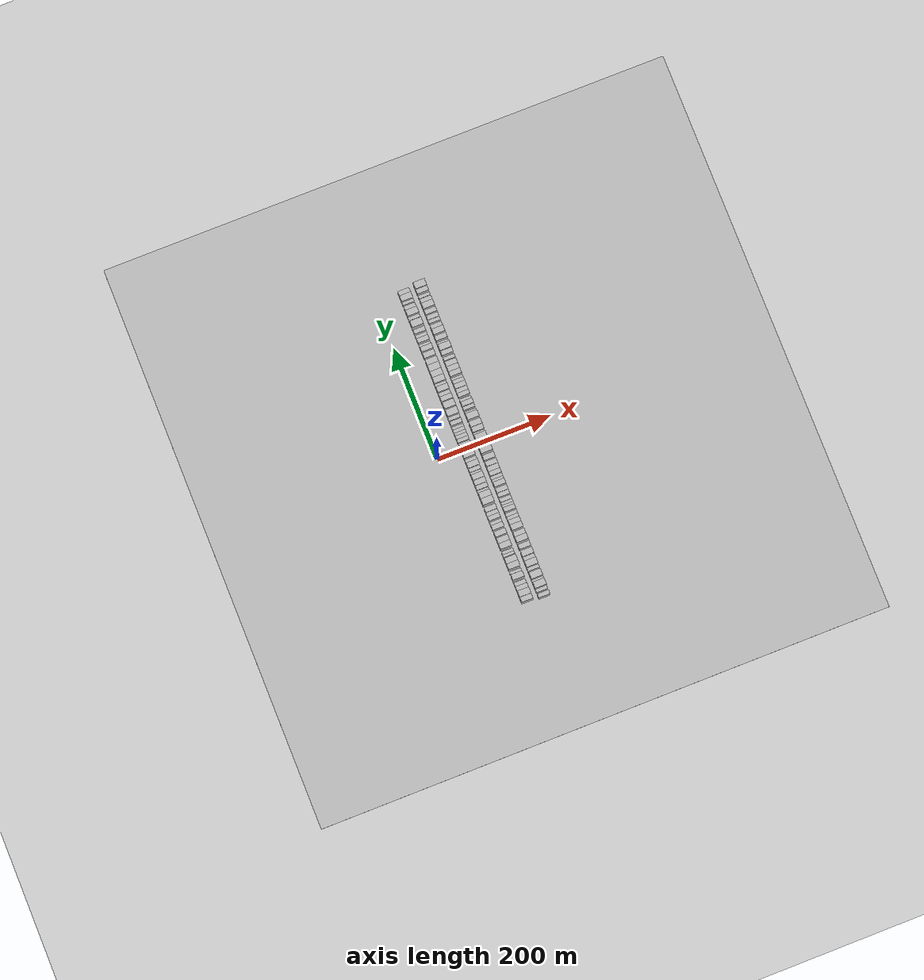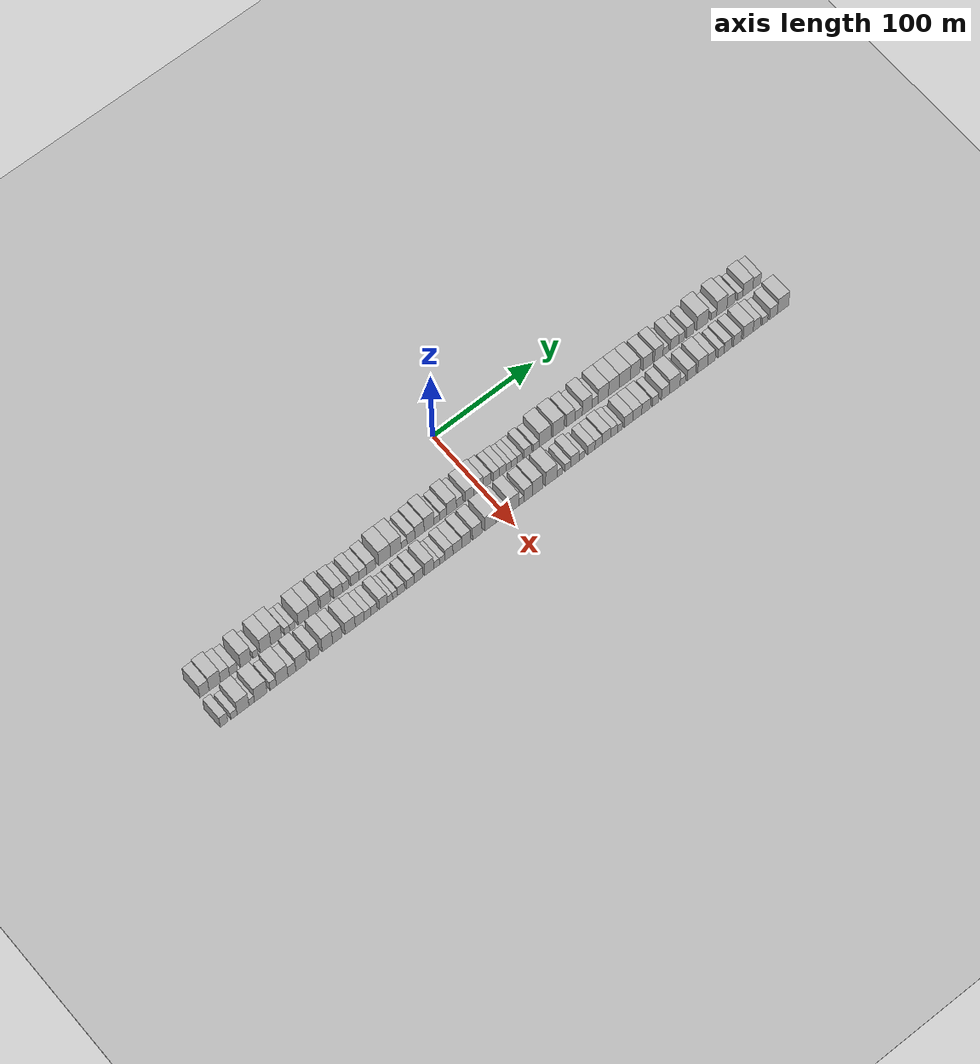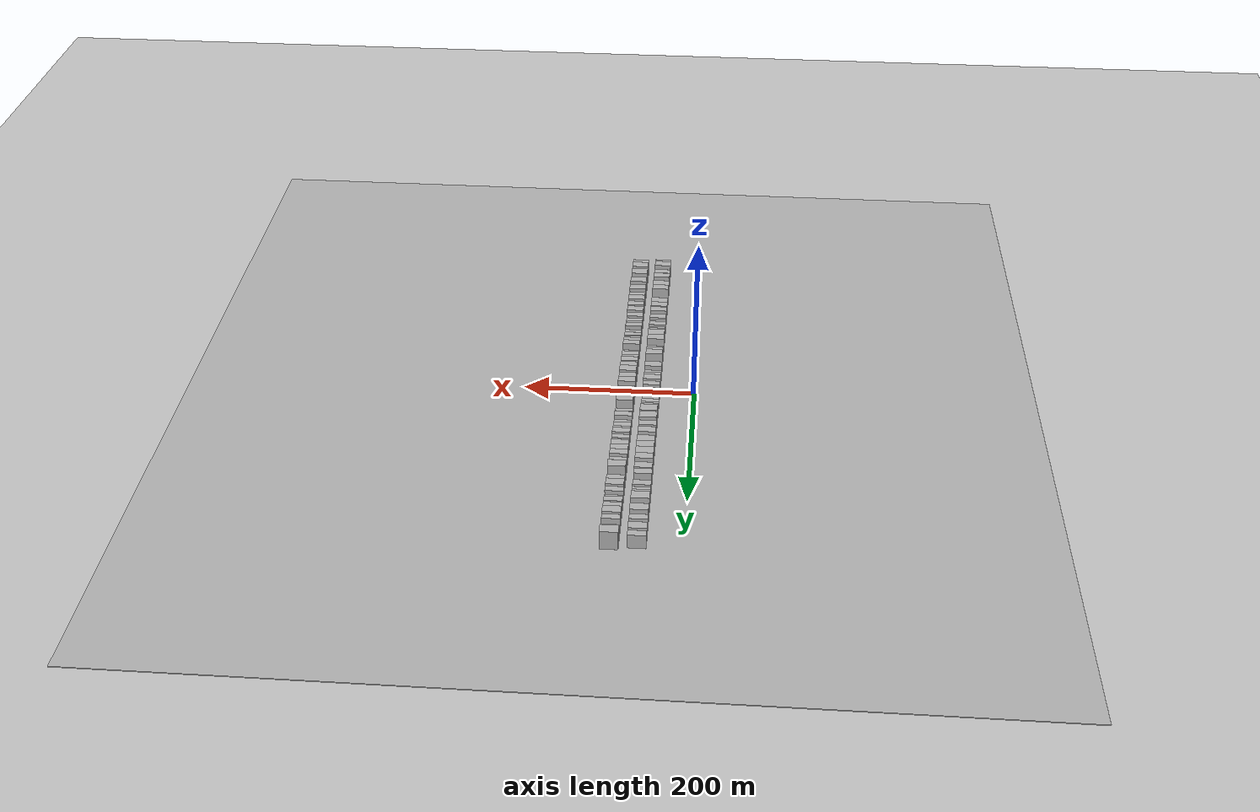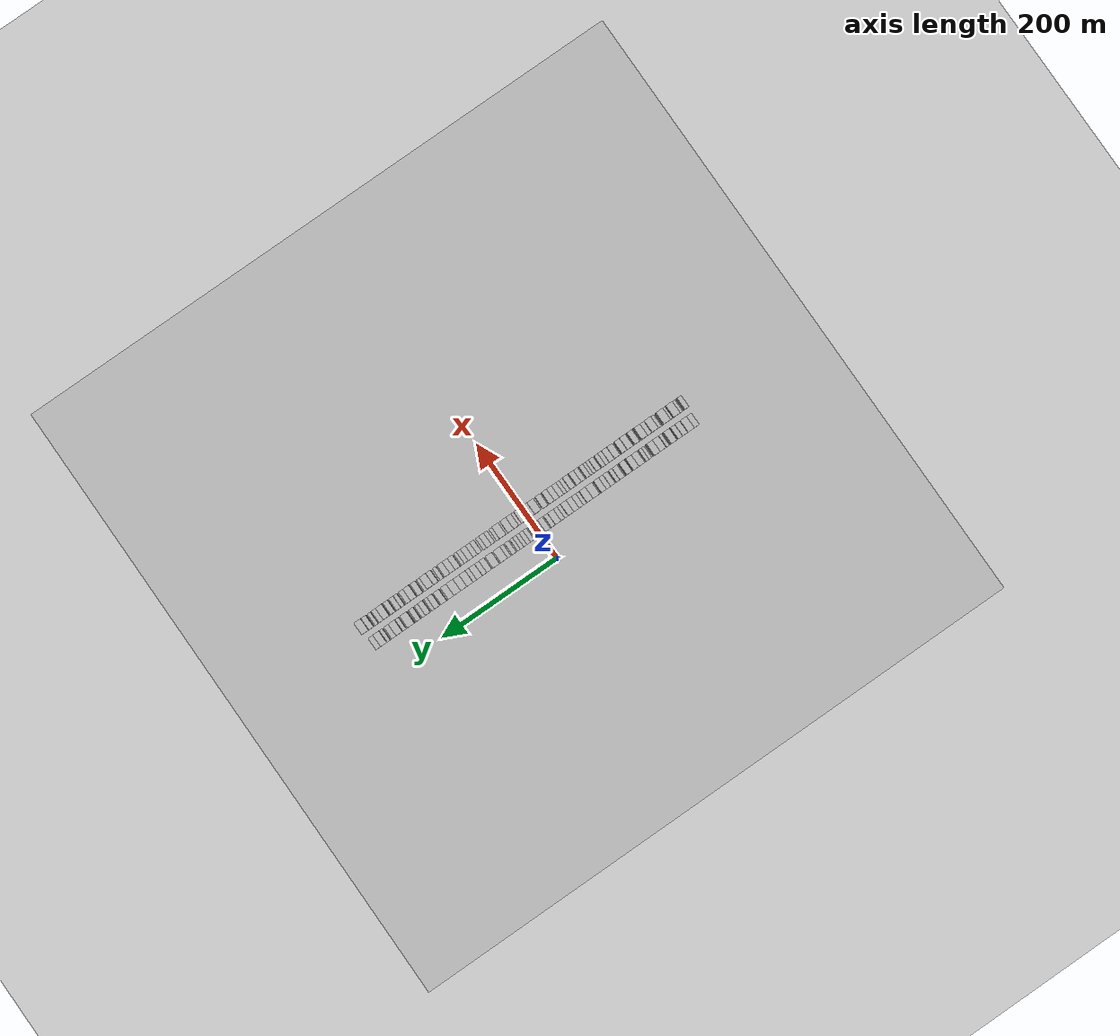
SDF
<?xml version="1.0" encoding="utf-8"?>

<sdf version="1.6">

   <world name="default">

      <gui fullscreen="0">

         <camera name="user_camera">

            <pose>-15 0 4.57585 0 0 0</pose>

            <view_controller>orbit</view_controller>

         </camera>

      </gui>

      <scene>

         <sky>

           <clouds>

             <speed>12</speed>

           </clouds>

         </sky>

         <ambient>0.4 0.4 0.4 1</ambient>

         <background>0.7 0.7 0.7 1</background>

         <shadows>1</shadows>

      </scene>

      <gravity>0 0 -9.8066</gravity>

      <magnetic_field>6e-06 2.3e-05 -4.2e-05</magnetic_field>

      <physics default="0" name="default_physics" type="ode">

         <ode>

            <solver>

               <type>quick</type>

               <iters>10</iters>

               <sor>1.0</sor>

               <use_dynamic_moi_rescaling>0</use_dynamic_moi_rescaling>

            </solver>

            <constraints>

               <cfm>0</cfm>

               <erp>0.2</erp>

               <contact_max_correcting_vel>100</contact_max_correcting_vel>

               <contact_surface_layer>0.001</contact_surface_layer>

            </constraints>

         </ode>

         <max_step_size>0.004</max_step_size>

         <real_time_factor>1</real_time_factor>

         <real_time_update_rate>250</real_time_update_rate>

      </physics>

      <light name="sun" type="directional">

         <cast_shadows>1</cast_shadows>

         <pose>0 0 10 0 0 0</pose>

         <diffuse>0.8 0.8 0.8 1</diffuse>

         <specular>0.2 0.2 0.2 1</specular>

         <attenuation>

            <range>1000</range>

            <constant>0.9</constant>

            <linear>0.01</linear>

            <quadratic>0.001</quadratic>

         </attenuation>

         <direction>-0.5 0.1 -0.9</direction>

      </light>

      <include>

         <name>ground_plane_1</name>

         <uri>model://HANNAS_ground_plane</uri>

         <pose>0 0 0  0 0 0</pose>

      </include>

      <include>

         <name>ground_plane_2</name>

         <uri>model://HANNAS_ground_plane</uri>

         <pose>100 0 0  0 0 0</pose>

      </include>

      <model name="building_1">

         <static>1</static>

         <pose frame="">50.0000 -270.5878 0 0.000000 0.000000 0.000000</pose>

         <link name="link">

            <pose frame="">0 0 10.50 0 0 0</pose>

            <collision name="collision">

               <geometry>

                  <box>

                     <size>20.0000 8.8244 21.0000</size>

                  </box>

               </geometry>

               <max_contacts>10</max_contacts>

               <surface>

                  <contact>

                     <ode/>

                  </contact>

                  <bounce/>

                  <friction>

                     <torsional>

                        <ode/>

                     </torsional>

                     <ode/>

                  </friction>

               </surface>

            </collision>

            <visual name="visual">

               <cast_shadows>0</cast_shadows>

               <geometry>

                  <box>

                     <size>20.0000 8.8244 21.0000</size>

                  </box>

               </geometry>

               <material>

                  <script>

                     <uri>model://HANNAS_wall/materials/scripts</uri>

                     <uri>model://HANNAS_wall/materials/textures</uri>

                     <name>vrc/HANNAS_wall</name>

                  </script>

               </material>

            </visual>

            <self_collide>0</self_collide>

            <enable_wind>0</enable_wind>

            <kinematic>0</kinematic>

         </link>

      </model>

      <model name="building_2">

         <static>1</static>

         <pose frame="">50.0000 -260.7174 0 0.000000 0.000000 0.000000</pose>

         <link name="link">

            <pose frame="">0 0 12.00 0 0 0</pose>

            <collision name="collision">

               <geometry>

                  <box>

                     <size>20.0000 10.9165 24.0000</size>

                  </box>

               </geometry>

               <max_contacts>10</max_contacts>

               <surface>

                  <contact>

                     <ode/>

                  </contact>

                  <bounce/>

                  <friction>

                     <torsional>

                        <ode/>

                     </torsional>

                     <ode/>

                  </friction>

               </surface>

            </collision>

            <visual name="visual">

               <cast_shadows>0</cast_shadows>

               <geometry>

                  <box>

                     <size>20.0000 10.9165 24.0000</size>

                  </box>

               </geometry>

               <material>

                  <script>

                     <uri>model://HANNAS_wall/materials/scripts</uri>

                     <uri>model://HANNAS_wall/materials/textures</uri>

                     <name>vrc/HANNAS_wall</name>

                  </script>

               </material>

            </visual>

            <self_collide>0</self_collide>

            <enable_wind>0</enable_wind>

            <kinematic>0</kinematic>

         </link>

      </model>

      <model name="building_3">

         <static>1</static>

         <pose frame="">50.0000 -250.9753 0 0.000000 0.000000 0.000000</pose>

         <link name="link">

            <pose frame="">0 0 9.00 0 0 0</pose>

            <collision name="collision">

               <geometry>

                  <box>

                     <size>20.0000 8.5676 18.0000</size>

                  </box>

               </geometry>

               <max_contacts>10</max_contacts>

               <surface>

                  <contact>

                     <ode/>

                  </contact>

                  <bounce/>

                  <friction>

                     <torsional>

                        <ode/>

                     </torsional>

                     <ode/>

                  </friction>

               </surface>

            </collision>

            <visual name="visual">

               <cast_shadows>0</cast_shadows>

               <geometry>

                  <box>

                     <size>20.0000 8.5676 18.0000</size>

                  </box>

               </geometry>

               <material>

                  <script>

                     <uri>model://HANNAS_wall/materials/scripts</uri>

                     <uri>model://HANNAS_wall/materials/textures</uri>

                     <name>vrc/HANNAS_wall</name>

                  </script>

               </material>

            </visual>

            <self_collide>0</self_collide>

            <enable_wind>0</enable_wind>

            <kinematic>0</kinematic>

         </link>

      </model>

      <model name="building_4">

         <static>1</static>

         <pose frame="">50.0000 -242.9473 0 0.000000 0.000000 0.000000</pose>

         <link name="link">

            <pose frame="">0 0 7.50 0 0 0</pose>

            <collision name="collision">

               <geometry>

                  <box>

                     <size>20.0000 7.4884 15.0000</size>

                  </box>

               </geometry>

               <max_contacts>10</max_contacts>

               <surface>

                  <contact>

                     <ode/>

                  </contact>

                  <bounce/>

                  <friction>

                     <torsional>

                        <ode/>

                     </torsional>

                     <ode/>

                  </friction>

               </surface>

            </collision>

            <visual name="visual">

               <cast_shadows>0</cast_shadows>

               <geometry>

                  <box>

                     <size>20.0000 7.4884 15.0000</size>

                  </box>

               </geometry>

               <material>

                  <script>

                     <uri>model://HANNAS_wall/materials/scripts</uri>

                     <uri>model://HANNAS_wall/materials/textures</uri>

                     <name>vrc/HANNAS_wall</name>

                  </script>

               </material>

            </visual>

            <self_collide>0</self_collide>

            <enable_wind>0</enable_wind>

            <kinematic>0</kinematic>

         </link>

      </model>

      <model name="building_5">

         <static>1</static>

         <pose frame="">50.0000 -231.1971 0 0.000000 0.000000 0.000000</pose>

         <link name="link">

            <pose frame="">0 0 12.00 0 0 0</pose>

            <collision name="collision">

               <geometry>

                  <box>

                     <size>20.0000 10.0120 24.0000</size>

                  </box>

               </geometry>

               <max_contacts>10</max_contacts>

               <surface>

                  <contact>

                     <ode/>

                  </contact>

                  <bounce/>

                  <friction>

                     <torsional>

                        <ode/>

                     </torsional>

                     <ode/>

                  </friction>

               </surface>

            </collision>

            <visual name="visual">

               <cast_shadows>0</cast_shadows>

               <geometry>

                  <box>

                     <size>20.0000 10.0120 24.0000</size>

                  </box>

               </geometry>

               <material>

                  <script>

                     <uri>model://HANNAS_wall/materials/scripts</uri>

                     <uri>model://HANNAS_wall/materials/textures</uri>

                     <name>vrc/HANNAS_wall</name>

                  </script>

               </material>

            </visual>

            <self_collide>0</self_collide>

            <enable_wind>0</enable_wind>

            <kinematic>0</kinematic>

         </link>

      </model>

      <model name="building_6">

         <static>1</static>

         <pose frame="">50.0000 -221.7817 0 0.000000 0.000000 0.000000</pose>

         <link name="link">

            <pose frame="">0 0 6.00 0 0 0</pose>

            <collision name="collision">

               <geometry>

                  <box>

                     <size>20.0000 4.8187 12.0000</size>

                  </box>

               </geometry>

               <max_contacts>10</max_contacts>

               <surface>

                  <contact>

                     <ode/>

                  </contact>

                  <bounce/>

                  <friction>

                     <torsional>

                        <ode/>

                     </torsional>

                     <ode/>

                  </friction>

               </surface>

            </collision>

            <visual name="visual">

               <cast_shadows>0</cast_shadows>

               <geometry>

                  <box>

                     <size>20.0000 4.8187 12.0000</size>

                  </box>

               </geometry>

               <material>

                  <script>

                     <uri>model://HANNAS_wall/materials/scripts</uri>

                     <uri>model://HANNAS_wall/materials/textures</uri>

                     <name>vrc/HANNAS_wall</name>

                  </script>

               </material>

            </visual>

            <self_collide>0</self_collide>

            <enable_wind>0</enable_wind>

            <kinematic>0</kinematic>

         </link>

      </model>

      <model name="building_7">

         <static>1</static>

         <pose frame="">50.0000 -212.1964 0 0.000000 0.000000 0.000000</pose>

         <link name="link">

            <pose frame="">0 0 12.00 0 0 0</pose>

            <collision name="collision">

               <geometry>

                  <box>

                     <size>20.0000 10.3518 24.0000</size>

                  </box>

               </geometry>

               <max_contacts>10</max_contacts>

               <surface>

                  <contact>

                     <ode/>

                  </contact>

                  <bounce/>

                  <friction>

                     <torsional>

                        <ode/>

                     </torsional>

                     <ode/>

                  </friction>

               </surface>

            </collision>

            <visual name="visual">

               <cast_shadows>0</cast_shadows>

               <geometry>

                  <box>

                     <size>20.0000 10.3518 24.0000</size>

                  </box>

               </geometry>

               <material>

                  <script>

                     <uri>model://HANNAS_wall/materials/scripts</uri>

                     <uri>model://HANNAS_wall/materials/textures</uri>

                     <name>vrc/HANNAS_wall</name>

                  </script>

               </material>

            </visual>

            <self_collide>0</self_collide>

            <enable_wind>0</enable_wind>

            <kinematic>0</kinematic>

         </link>

      </model>

      <model name="building_8">

         <static>1</static>

         <pose frame="">50.0000 -201.9319 0 0.000000 0.000000 0.000000</pose>

         <link name="link">

            <pose frame="">0 0 12.00 0 0 0</pose>

            <collision name="collision">

               <geometry>

                  <box>

                     <size>20.0000 10.1771 24.0000</size>

                  </box>

               </geometry>

               <max_contacts>10</max_contacts>

               <surface>

                  <contact>

                     <ode/>

                  </contact>

                  <bounce/>

                  <friction>

                     <torsional>

                        <ode/>

                     </torsional>

                     <ode/>

                  </friction>

               </surface>

            </collision>

            <visual name="visual">

               <cast_shadows>0</cast_shadows>

               <geometry>

                  <box>

                     <size>20.0000 10.1771 24.0000</size>

                  </box>

               </geometry>

               <material>

                  <script>

                     <uri>model://HANNAS_wall/materials/scripts</uri>

                     <uri>model://HANNAS_wall/materials/textures</uri>

                     <name>vrc/HANNAS_wall</name>

                  </script>

               </material>

            </visual>

            <self_collide>0</self_collide>

            <enable_wind>0</enable_wind>

            <kinematic>0</kinematic>

         </link>

      </model>

      <model name="building_9">

         <static>1</static>

         <pose frame="">50.0000 -191.3443 0 0.000000 0.000000 0.000000</pose>

         <link name="link">

            <pose frame="">0 0 6.00 0 0 0</pose>

            <collision name="collision">

               <geometry>

                  <box>

                     <size>20.0000 4.9982 12.0000</size>

                  </box>

               </geometry>

               <max_contacts>10</max_contacts>

               <surface>

                  <contact>

                     <ode/>

                  </contact>

                  <bounce/>

                  <friction>

                     <torsional>

                        <ode/>

                     </torsional>

                     <ode/>

                  </friction>

               </surface>

            </collision>

            <visual name="visual">

               <cast_shadows>0</cast_shadows>

               <geometry>

                  <box>

                     <size>20.0000 4.9982 12.0000</size>

                  </box>

               </geometry>

               <material>

                  <script>

                     <uri>model://HANNAS_wall/materials/scripts</uri>

                     <uri>model://HANNAS_wall/materials/textures</uri>

                     <name>vrc/HANNAS_wall</name>

                  </script>

               </material>

            </visual>

            <self_collide>0</self_collide>

            <enable_wind>0</enable_wind>

            <kinematic>0</kinematic>

         </link>

      </model>

      <model name="building_10">

         <static>1</static>

         <pose frame="">50.0000 -186.2483 0 0.000000 0.000000 0.000000</pose>

         <link name="link">

            <pose frame="">0 0 6.00 0 0 0</pose>

            <collision name="collision">

               <geometry>

                  <box>

                     <size>20.0000 5.1938 12.0000</size>

                  </box>

               </geometry>

               <max_contacts>10</max_contacts>

               <surface>

                  <contact>

                     <ode/>

                  </contact>

                  <bounce/>

                  <friction>

                     <torsional>

                        <ode/>

                     </torsional>

                     <ode/>

                  </friction>

               </surface>

            </collision>

            <visual name="visual">

               <cast_shadows>0</cast_shadows>

               <geometry>

                  <box>

                     <size>20.0000 5.1938 12.0000</size>

                  </box>

               </geometry>

               <material>

                  <script>

                     <uri>model://HANNAS_wall/materials/scripts</uri>

                     <uri>model://HANNAS_wall/materials/textures</uri>

                     <name>vrc/HANNAS_wall</name>

                  </script>

               </material>

            </visual>

            <self_collide>0</self_collide>

            <enable_wind>0</enable_wind>

            <kinematic>0</kinematic>

         </link>

      </model>

      <model name="building_11">

         <static>1</static>

         <pose frame="">50.0000 -175.5425 0 0.000000 0.000000 0.000000</pose>

         <link name="link">

            <pose frame="">0 0 10.50 0 0 0</pose>

            <collision name="collision">

               <geometry>

                  <box>

                     <size>20.0000 10.2178 21.0000</size>

                  </box>

               </geometry>

               <max_contacts>10</max_contacts>

               <surface>

                  <contact>

                     <ode/>

                  </contact>

                  <bounce/>

                  <friction>

                     <torsional>

                        <ode/>

                     </torsional>

                     <ode/>

                  </friction>

               </surface>

            </collision>

            <visual name="visual">

               <cast_shadows>0</cast_shadows>

               <geometry>

                  <box>

                     <size>20.0000 10.2178 21.0000</size>

                  </box>

               </geometry>

               <material>

                  <script>

                     <uri>model://HANNAS_wall/materials/scripts</uri>

                     <uri>model://HANNAS_wall/materials/textures</uri>

                     <name>vrc/HANNAS_wall</name>

                  </script>

               </material>

            </visual>

            <self_collide>0</self_collide>

            <enable_wind>0</enable_wind>

            <kinematic>0</kinematic>

         </link>

      </model>

      <model name="building_12">

         <static>1</static>

         <pose frame="">50.0000 -165.5731 0 0.000000 0.000000 0.000000</pose>

         <link name="link">

            <pose frame="">0 0 10.50 0 0 0</pose>

            <collision name="collision">

               <geometry>

                  <box>

                     <size>20.0000 9.7209 21.0000</size>

                  </box>

               </geometry>

               <max_contacts>10</max_contacts>

               <surface>

                  <contact>

                     <ode/>

                  </contact>

                  <bounce/>

                  <friction>

                     <torsional>

                        <ode/>

                     </torsional>

                     <ode/>

                  </friction>

               </surface>

            </collision>

            <visual name="visual">

               <cast_shadows>0</cast_shadows>

               <geometry>

                  <box>

                     <size>20.0000 9.7209 21.0000</size>

                  </box>

               </geometry>

               <material>

                  <script>

                     <uri>model://HANNAS_wall/materials/scripts</uri>

                     <uri>model://HANNAS_wall/materials/textures</uri>

                     <name>vrc/HANNAS_wall</name>

                  </script>

               </material>

            </visual>

            <self_collide>0</self_collide>

            <enable_wind>0</enable_wind>

            <kinematic>0</kinematic>

         </link>

      </model>

      <model name="building_13">

         <static>1</static>

         <pose frame="">50.0000 -153.9268 0 0.000000 0.000000 0.000000</pose>

         <link name="link">

            <pose frame="">0 0 10.50 0 0 0</pose>

            <collision name="collision">

               <geometry>

                  <box>

                     <size>20.0000 9.5718 21.0000</size>

                  </box>

               </geometry>

               <max_contacts>10</max_contacts>

               <surface>

                  <contact>

                     <ode/>

                  </contact>

                  <bounce/>

                  <friction>

                     <torsional>

                        <ode/>

                     </torsional>

                     <ode/>

                  </friction>

               </surface>

            </collision>

            <visual name="visual">

               <cast_shadows>0</cast_shadows>

               <geometry>

                  <box>

                     <size>20.0000 9.5718 21.0000</size>

                  </box>

               </geometry>

               <material>

                  <script>

                     <uri>model://HANNAS_wall/materials/scripts</uri>

                     <uri>model://HANNAS_wall/materials/textures</uri>

                     <name>vrc/HANNAS_wall</name>

                  </script>

               </material>

            </visual>

            <self_collide>0</self_collide>

            <enable_wind>0</enable_wind>

            <kinematic>0</kinematic>

         </link>

      </model>

      <model name="building_14">

         <static>1</static>

         <pose frame="">50.0000 -141.8351 0 0.000000 0.000000 0.000000</pose>

         <link name="link">

            <pose frame="">0 0 9.00 0 0 0</pose>

            <collision name="collision">

               <geometry>

                  <box>

                     <size>20.0000 8.6117 18.0000</size>

                  </box>

               </geometry>

               <max_contacts>10</max_contacts>

               <surface>

                  <contact>

                     <ode/>

                  </contact>

                  <bounce/>

                  <friction>

                     <torsional>

                        <ode/>

                     </torsional>

                     <ode/>

                  </friction>

               </surface>

            </collision>

            <visual name="visual">

               <cast_shadows>0</cast_shadows>

               <geometry>

                  <box>

                     <size>20.0000 8.6117 18.0000</size>

                  </box>

               </geometry>

               <material>

                  <script>

                     <uri>model://HANNAS_wall/materials/scripts</uri>

                     <uri>model://HANNAS_wall/materials/textures</uri>

                     <name>vrc/HANNAS_wall</name>

                  </script>

               </material>

            </visual>

            <self_collide>0</self_collide>

            <enable_wind>0</enable_wind>

            <kinematic>0</kinematic>

         </link>

      </model>

      <model name="building_15">

         <static>1</static>

         <pose frame="">50.0000 -134.5054 0 0.000000 0.000000 0.000000</pose>

         <link name="link">

            <pose frame="">0 0 7.50 0 0 0</pose>

            <collision name="collision">

               <geometry>

                  <box>

                     <size>20.0000 6.0475 15.0000</size>

                  </box>

               </geometry>

               <max_contacts>10</max_contacts>

               <surface>

                  <contact>

                     <ode/>

                  </contact>

                  <bounce/>

                  <friction>

                     <torsional>

                        <ode/>

                     </torsional>

                     <ode/>

                  </friction>

               </surface>

            </collision>

            <visual name="visual">

               <cast_shadows>0</cast_shadows>

               <geometry>

                  <box>

                     <size>20.0000 6.0475 15.0000</size>

                  </box>

               </geometry>

               <material>

                  <script>

                     <uri>model://HANNAS_wall/materials/scripts</uri>

                     <uri>model://HANNAS_wall/materials/textures</uri>

                     <name>vrc/HANNAS_wall</name>

                  </script>

               </material>

            </visual>

            <self_collide>0</self_collide>

            <enable_wind>0</enable_wind>

            <kinematic>0</kinematic>

         </link>

      </model>

      <model name="building_16">

         <static>1</static>

         <pose frame="">50.0000 -125.5305 0 0.000000 0.000000 0.000000</pose>

         <link name="link">

            <pose frame="">0 0 9.00 0 0 0</pose>

            <collision name="collision">

               <geometry>

                  <box>

                     <size>20.0000 7.9024 18.0000</size>

                  </box>

               </geometry>

               <max_contacts>10</max_contacts>

               <surface>

                  <contact>

                     <ode/>

                  </contact>

                  <bounce/>

                  <friction>

                     <torsional>

                        <ode/>

                     </torsional>

                     <ode/>

                  </friction>

               </surface>

            </collision>

            <visual name="visual">

               <cast_shadows>0</cast_shadows>

               <geometry>

                  <box>

                     <size>20.0000 7.9024 18.0000</size>

                  </box>

               </geometry>

               <material>

                  <script>

                     <uri>model://HANNAS_wall/materials/scripts</uri>

                     <uri>model://HANNAS_wall/materials/textures</uri>

                     <name>vrc/HANNAS_wall</name>

                  </script>

               </material>

            </visual>

            <self_collide>0</self_collide>

            <enable_wind>0</enable_wind>

            <kinematic>0</kinematic>

         </link>

      </model>

      <model name="building_17">

         <static>1</static>

         <pose frame="">50.0000 -117.8935 0 0.000000 0.000000 0.000000</pose>

         <link name="link">

            <pose frame="">0 0 7.50 0 0 0</pose>

            <collision name="collision">

               <geometry>

                  <box>

                     <size>20.0000 7.3716 15.0000</size>

                  </box>

               </geometry>

               <max_contacts>10</max_contacts>

               <surface>

                  <contact>

                     <ode/>

                  </contact>

                  <bounce/>

                  <friction>

                     <torsional>

                        <ode/>

                     </torsional>

                     <ode/>

                  </friction>

               </surface>

            </collision>

            <visual name="visual">

               <cast_shadows>0</cast_shadows>

               <geometry>

                  <box>

                     <size>20.0000 7.3716 15.0000</size>

                  </box>

               </geometry>

               <material>

                  <script>

                     <uri>model://HANNAS_wall/materials/scripts</uri>

                     <uri>model://HANNAS_wall/materials/textures</uri>

                     <name>vrc/HANNAS_wall</name>

                  </script>

               </material>

            </visual>

            <self_collide>0</self_collide>

            <enable_wind>0</enable_wind>

            <kinematic>0</kinematic>

         </link>

      </model>

      <model name="building_18">

         <static>1</static>

         <pose frame="">50.0000 -109.7421 0 0.000000 0.000000 0.000000</pose>

         <link name="link">

            <pose frame="">0 0 9.00 0 0 0</pose>

            <collision name="collision">

               <geometry>

                  <box>

                     <size>20.0000 8.9311 18.0000</size>

                  </box>

               </geometry>

               <max_contacts>10</max_contacts>

               <surface>

                  <contact>

                     <ode/>

                  </contact>

                  <bounce/>

                  <friction>

                     <torsional>

                        <ode/>

                     </torsional>

                     <ode/>

                  </friction>

               </surface>

            </collision>

            <visual name="visual">

               <cast_shadows>0</cast_shadows>

               <geometry>

                  <box>

                     <size>20.0000 8.9311 18.0000</size>

                  </box>

               </geometry>

               <material>

                  <script>

                     <uri>model://HANNAS_wall/materials/scripts</uri>

                     <uri>model://HANNAS_wall/materials/textures</uri>

                     <name>vrc/HANNAS_wall</name>

                  </script>

               </material>

            </visual>

            <self_collide>0</self_collide>

            <enable_wind>0</enable_wind>

            <kinematic>0</kinematic>

         </link>

      </model>

      <model name="building_19">

         <static>1</static>

         <pose frame="">50.0000 -96.4635 0 0.000000 0.000000 0.000000</pose>

         <link name="link">

            <pose frame="">0 0 12.00 0 0 0</pose>

            <collision name="collision">

               <geometry>

                  <box>

                     <size>20.0000 11.6262 24.0000</size>

                  </box>

               </geometry>

               <max_contacts>10</max_contacts>

               <surface>

                  <contact>

                     <ode/>

                  </contact>

                  <bounce/>

                  <friction>

                     <torsional>

                        <ode/>

                     </torsional>

                     <ode/>

                  </friction>

               </surface>

            </collision>

            <visual name="visual">

               <cast_shadows>0</cast_shadows>

               <geometry>

                  <box>

                     <size>20.0000 11.6262 24.0000</size>

                  </box>

               </geometry>

               <material>

                  <script>

                     <uri>model://HANNAS_wall/materials/scripts</uri>

                     <uri>model://HANNAS_wall/materials/textures</uri>

                     <name>vrc/HANNAS_wall</name>

                  </script>

               </material>

            </visual>

            <self_collide>0</self_collide>

            <enable_wind>0</enable_wind>

            <kinematic>0</kinematic>

         </link>

      </model>

      <model name="building_20">

         <static>1</static>

         <pose frame="">50.0000 -85.4118 0 0.000000 0.000000 0.000000</pose>

         <link name="link">

            <pose frame="">0 0 12.00 0 0 0</pose>

            <collision name="collision">

               <geometry>

                  <box>

                     <size>20.0000 10.4770 24.0000</size>

                  </box>

               </geometry>

               <max_contacts>10</max_contacts>

               <surface>

                  <contact>

                     <ode/>

                  </contact>

                  <bounce/>

                  <friction>

                     <torsional>

                        <ode/>

                     </torsional>

                     <ode/>

                  </friction>

               </surface>

            </collision>

            <visual name="visual">

               <cast_shadows>0</cast_shadows>

               <geometry>

                  <box>

                     <size>20.0000 10.4770 24.0000</size>

                  </box>

               </geometry>

               <material>

                  <script>

                     <uri>model://HANNAS_wall/materials/scripts</uri>

                     <uri>model://HANNAS_wall/materials/textures</uri>

                     <name>vrc/HANNAS_wall</name>

                  </script>

               </material>

            </visual>

            <self_collide>0</self_collide>

            <enable_wind>0</enable_wind>

            <kinematic>0</kinematic>

         </link>

      </model>

      <model name="building_21">

         <static>1</static>

         <pose frame="">50.0000 -77.3133 0 0.000000 0.000000 0.000000</pose>

         <link name="link">

            <pose frame="">0 0 6.00 0 0 0</pose>

            <collision name="collision">

               <geometry>

                  <box>

                     <size>20.0000 5.7202 12.0000</size>

                  </box>

               </geometry>

               <max_contacts>10</max_contacts>

               <surface>

                  <contact>

                     <ode/>

                  </contact>

                  <bounce/>

                  <friction>

                     <torsional>

                        <ode/>

                     </torsional>

                     <ode/>

                  </friction>

               </surface>

            </collision>

            <visual name="visual">

               <cast_shadows>0</cast_shadows>

               <geometry>

                  <box>

                     <size>20.0000 5.7202 12.0000</size>

                  </box>

               </geometry>

               <material>

                  <script>

                     <uri>model://HANNAS_wall/materials/scripts</uri>

                     <uri>model://HANNAS_wall/materials/textures</uri>

                     <name>vrc/HANNAS_wall</name>

                  </script>

               </material>

            </visual>

            <self_collide>0</self_collide>

            <enable_wind>0</enable_wind>

            <kinematic>0</kinematic>

         </link>

      </model>

      <model name="building_22">

         <static>1</static>

         <pose frame="">50.0000 -70.5814 0 0.000000 0.000000 0.000000</pose>

         <link name="link">

            <pose frame="">0 0 9.00 0 0 0</pose>

            <collision name="collision">

               <geometry>

                  <box>

                     <size>20.0000 7.7435 18.0000</size>

                  </box>

               </geometry>

               <max_contacts>10</max_contacts>

               <surface>

                  <contact>

                     <ode/>

                  </contact>

                  <bounce/>

                  <friction>

                     <torsional>

                        <ode/>

                     </torsional>

                     <ode/>

                  </friction>

               </surface>

            </collision>

            <visual name="visual">

               <cast_shadows>0</cast_shadows>

               <geometry>

                  <box>

                     <size>20.0000 7.7435 18.0000</size>

                  </box>

               </geometry>

               <material>

                  <script>

                     <uri>model://HANNAS_wall/materials/scripts</uri>

                     <uri>model://HANNAS_wall/materials/textures</uri>

                     <name>vrc/HANNAS_wall</name>

                  </script>

               </material>

            </visual>

            <self_collide>0</self_collide>

            <enable_wind>0</enable_wind>

            <kinematic>0</kinematic>

         </link>

      </model>

      <model name="building_23">

         <static>1</static>

         <pose frame="">50.0000 -62.1440 0 0.000000 0.000000 0.000000</pose>

         <link name="link">

            <pose frame="">0 0 10.50 0 0 0</pose>

            <collision name="collision">

               <geometry>

                  <box>

                     <size>20.0000 9.1313 21.0000</size>

                  </box>

               </geometry>

               <max_contacts>10</max_contacts>

               <surface>

                  <contact>

                     <ode/>

                  </contact>

                  <bounce/>

                  <friction>

                     <torsional>

                        <ode/>

                     </torsional>

                     <ode/>

                  </friction>

               </surface>

            </collision>

            <visual name="visual">

               <cast_shadows>0</cast_shadows>

               <geometry>

                  <box>

                     <size>20.0000 9.1313 21.0000</size>

                  </box>

               </geometry>

               <material>

                  <script>

                     <uri>model://HANNAS_wall/materials/scripts</uri>

                     <uri>model://HANNAS_wall/materials/textures</uri>

                     <name>vrc/HANNAS_wall</name>

                  </script>

               </material>

            </visual>

            <self_collide>0</self_collide>

            <enable_wind>0</enable_wind>

            <kinematic>0</kinematic>

         </link>

      </model>

      <model name="building_24">

         <static>1</static>

         <pose frame="">50.0000 -52.6865 0 0.000000 0.000000 0.000000</pose>

         <link name="link">

            <pose frame="">0 0 12.00 0 0 0</pose>

            <collision name="collision">

               <geometry>

                  <box>

                     <size>20.0000 9.7836 24.0000</size>

                  </box>

               </geometry>

               <max_contacts>10</max_contacts>

               <surface>

                  <contact>

                     <ode/>

                  </contact>

                  <bounce/>

                  <friction>

                     <torsional>

                        <ode/>

                     </torsional>

                     <ode/>

                  </friction>

               </surface>

            </collision>

            <visual name="visual">

               <cast_shadows>0</cast_shadows>

               <geometry>

                  <box>

                     <size>20.0000 9.7836 24.0000</size>

                  </box>

               </geometry>

               <material>

                  <script>

                     <uri>model://HANNAS_wall/materials/scripts</uri>

                     <uri>model://HANNAS_wall/materials/textures</uri>

                     <name>vrc/HANNAS_wall</name>

                  </script>

               </material>

            </visual>

            <self_collide>0</self_collide>

            <enable_wind>0</enable_wind>

            <kinematic>0</kinematic>

         </link>

      </model>

      <model name="building_25">

         <static>1</static>

         <pose frame="">50.0000 -44.9658 0 0.000000 0.000000 0.000000</pose>

         <link name="link">

            <pose frame="">0 0 6.00 0 0 0</pose>

            <collision name="collision">

               <geometry>

                  <box>

                     <size>20.0000 5.6578 12.0000</size>

                  </box>

               </geometry>

               <max_contacts>10</max_contacts>

               <surface>

                  <contact>

                     <ode/>

                  </contact>

                  <bounce/>

                  <friction>

                     <torsional>

                        <ode/>

                     </torsional>

                     <ode/>

                  </friction>

               </surface>

            </collision>

            <visual name="visual">

               <cast_shadows>0</cast_shadows>

               <geometry>

                  <box>

                     <size>20.0000 5.6578 12.0000</size>

                  </box>

               </geometry>

               <material>

                  <script>

                     <uri>model://HANNAS_wall/materials/scripts</uri>

                     <uri>model://HANNAS_wall/materials/textures</uri>

                     <name>vrc/HANNAS_wall</name>

                  </script>

               </material>

            </visual>

            <self_collide>0</self_collide>

            <enable_wind>0</enable_wind>

            <kinematic>0</kinematic>

         </link>

      </model>

      <model name="building_26">

         <static>1</static>

         <pose frame="">50.0000 -38.7752 0 0.000000 0.000000 0.000000</pose>

         <link name="link">

            <pose frame="">0 0 7.50 0 0 0</pose>

            <collision name="collision">

               <geometry>

                  <box>

                     <size>20.0000 6.7235 15.0000</size>

                  </box>

               </geometry>

               <max_contacts>10</max_contacts>

               <surface>

                  <contact>

                     <ode/>

                  </contact>

                  <bounce/>

                  <friction>

                     <torsional>

                        <ode/>

                     </torsional>

                     <ode/>

                  </friction>

               </surface>

            </collision>

            <visual name="visual">

               <cast_shadows>0</cast_shadows>

               <geometry>

                  <box>

                     <size>20.0000 6.7235 15.0000</size>

                  </box>

               </geometry>

               <material>

                  <script>

                     <uri>model://HANNAS_wall/materials/scripts</uri>

                     <uri>model://HANNAS_wall/materials/textures</uri>

                     <name>vrc/HANNAS_wall</name>

                  </script>

               </material>

            </visual>

            <self_collide>0</self_collide>

            <enable_wind>0</enable_wind>

            <kinematic>0</kinematic>

         </link>

      </model>

      <model name="building_27">

         <static>1</static>

         <pose frame="">50.0000 -30.5352 0 0.000000 0.000000 0.000000</pose>

         <link name="link">

            <pose frame="">0 0 10.50 0 0 0</pose>

            <collision name="collision">

               <geometry>

                  <box>

                     <size>20.0000 9.7567 21.0000</size>

                  </box>

               </geometry>

               <max_contacts>10</max_contacts>

               <surface>

                  <contact>

                     <ode/>

                  </contact>

                  <bounce/>

                  <friction>

                     <torsional>

                        <ode/>

                     </torsional>

                     <ode/>

                  </friction>

               </surface>

            </collision>

            <visual name="visual">

               <cast_shadows>0</cast_shadows>

               <geometry>

                  <box>

                     <size>20.0000 9.7567 21.0000</size>

                  </box>

               </geometry>

               <material>

                  <script>

                     <uri>model://HANNAS_wall/materials/scripts</uri>

                     <uri>model://HANNAS_wall/materials/textures</uri>

                     <name>vrc/HANNAS_wall</name>

                  </script>

               </material>

            </visual>

            <self_collide>0</self_collide>

            <enable_wind>0</enable_wind>

            <kinematic>0</kinematic>

         </link>

      </model>

      <model name="building_28">

         <static>1</static>

         <pose frame="">50.0000 -22.3069 0 0.000000 0.000000 0.000000</pose>

         <link name="link">

            <pose frame="">0 0 7.50 0 0 0</pose>

            <collision name="collision">

               <geometry>

                  <box>

                     <size>20.0000 6.6999 15.0000</size>

                  </box>

               </geometry>

               <max_contacts>10</max_contacts>

               <surface>

                  <contact>

                     <ode/>

                  </contact>

                  <bounce/>

                  <friction>

                     <torsional>

                        <ode/>

                     </torsional>

                     <ode/>

                  </friction>

               </surface>

            </collision>

            <visual name="visual">

               <cast_shadows>0</cast_shadows>

               <geometry>

                  <box>

                     <size>20.0000 6.6999 15.0000</size>

                  </box>

               </geometry>

               <material>

                  <script>

                     <uri>model://HANNAS_wall/materials/scripts</uri>

                     <uri>model://HANNAS_wall/materials/textures</uri>

                     <name>vrc/HANNAS_wall</name>

                  </script>

               </material>

            </visual>

            <self_collide>0</self_collide>

            <enable_wind>0</enable_wind>

            <kinematic>0</kinematic>

         </link>

      </model>

      <model name="building_29">

         <static>1</static>

         <pose frame="">50.0000 -12.6182 0 0.000000 0.000000 0.000000</pose>

         <link name="link">

            <pose frame="">0 0 9.00 0 0 0</pose>

            <collision name="collision">

               <geometry>

                  <box>

                     <size>20.0000 8.6775 18.0000</size>

                  </box>

               </geometry>

               <max_contacts>10</max_contacts>

               <surface>

                  <contact>

                     <ode/>

                  </contact>

                  <bounce/>

                  <friction>

                     <torsional>

                        <ode/>

                     </torsional>

                     <ode/>

                  </friction>

               </surface>

            </collision>

            <visual name="visual">

               <cast_shadows>0</cast_shadows>

               <geometry>

                  <box>

                     <size>20.0000 8.6775 18.0000</size>

                  </box>

               </geometry>

               <material>

                  <script>

                     <uri>model://HANNAS_wall/materials/scripts</uri>

                     <uri>model://HANNAS_wall/materials/textures</uri>

                     <name>vrc/HANNAS_wall</name>

                  </script>

               </material>

            </visual>

            <self_collide>0</self_collide>

            <enable_wind>0</enable_wind>

            <kinematic>0</kinematic>

         </link>

      </model>

      <model name="building_30">

         <static>1</static>

         <pose frame="">50.0000 -3.4968 0 0.000000 0.000000 0.000000</pose>

         <link name="link">

            <pose frame="">0 0 10.50 0 0 0</pose>

            <collision name="collision">

               <geometry>

                  <box>

                     <size>20.0000 9.5653 21.0000</size>

                  </box>

               </geometry>

               <max_contacts>10</max_contacts>

               <surface>

                  <contact>

                     <ode/>

                  </contact>

                  <bounce/>

                  <friction>

                     <torsional>

                        <ode/>

                     </torsional>

                     <ode/>

                  </friction>

               </surface>

            </collision>

            <visual name="visual">

               <cast_shadows>0</cast_shadows>

               <geometry>

                  <box>

                     <size>20.0000 9.5653 21.0000</size>

                  </box>

               </geometry>

               <material>

                  <script>

                     <uri>model://HANNAS_wall/materials/scripts</uri>

                     <uri>model://HANNAS_wall/materials/textures</uri>

                     <name>vrc/HANNAS_wall</name>

                  </script>

               </material>

            </visual>

            <self_collide>0</self_collide>

            <enable_wind>0</enable_wind>

            <kinematic>0</kinematic>

         </link>

      </model>

      <model name="building_31">

         <static>1</static>

         <pose frame="">50.0000 5.1058 0 0.000000 0.000000 0.000000</pose>

         <link name="link">

            <pose frame="">0 0 9.00 0 0 0</pose>

            <collision name="collision">

               <geometry>

                  <box>

                     <size>20.0000 7.6399 18.0000</size>

                  </box>

               </geometry>

               <max_contacts>10</max_contacts>

               <surface>

                  <contact>

                     <ode/>

                  </contact>

                  <bounce/>

                  <friction>

                     <torsional>

                        <ode/>

                     </torsional>

                     <ode/>

                  </friction>

               </surface>

            </collision>

            <visual name="visual">

               <cast_shadows>0</cast_shadows>

               <geometry>

                  <box>

                     <size>20.0000 7.6399 18.0000</size>

                  </box>

               </geometry>

               <material>

                  <script>

                     <uri>model://HANNAS_wall/materials/scripts</uri>

                     <uri>model://HANNAS_wall/materials/textures</uri>

                     <name>vrc/HANNAS_wall</name>

                  </script>

               </material>

            </visual>

            <self_collide>0</self_collide>

            <enable_wind>0</enable_wind>

            <kinematic>0</kinematic>

         </link>

      </model>

      <model name="building_32">

         <static>1</static>

         <pose frame="">50.0000 14.0946 0 0.000000 0.000000 0.000000</pose>

         <link name="link">

            <pose frame="">0 0 7.50 0 0 0</pose>

            <collision name="collision">

               <geometry>

                  <box>

                     <size>20.0000 6.3376 15.0000</size>

                  </box>

               </geometry>

               <max_contacts>10</max_contacts>

               <surface>

                  <contact>

                     <ode/>

                  </contact>

                  <bounce/>

                  <friction>

                     <torsional>

                        <ode/>

                     </torsional>

                     <ode/>

                  </friction>

               </surface>

            </collision>

            <visual name="visual">

               <cast_shadows>0</cast_shadows>

               <geometry>

                  <box>

                     <size>20.0000 6.3376 15.0000</size>

                  </box>

               </geometry>

               <material>

                  <script>

                     <uri>model://HANNAS_wall/materials/scripts</uri>

                     <uri>model://HANNAS_wall/materials/textures</uri>

                     <name>vrc/HANNAS_wall</name>

                  </script>

               </material>

            </visual>

            <self_collide>0</self_collide>

            <enable_wind>0</enable_wind>

            <kinematic>0</kinematic>

         </link>

      </model>

      <model name="building_33">

         <static>1</static>

         <pose frame="">50.0000 20.4826 0 0.000000 0.000000 0.000000</pose>

         <link name="link">

            <pose frame="">0 0 7.50 0 0 0</pose>

            <collision name="collision">

               <geometry>

                  <box>

                     <size>20.0000 6.4384 15.0000</size>

                  </box>

               </geometry>

               <max_contacts>10</max_contacts>

               <surface>

                  <contact>

                     <ode/>

                  </contact>

                  <bounce/>

                  <friction>

                     <torsional>

                        <ode/>

                     </torsional>

                     <ode/>

                  </friction>

               </surface>

            </collision>

            <visual name="visual">

               <cast_shadows>0</cast_shadows>

               <geometry>

                  <box>

                     <size>20.0000 6.4384 15.0000</size>

                  </box>

               </geometry>

               <material>

                  <script>

                     <uri>model://HANNAS_wall/materials/scripts</uri>

                     <uri>model://HANNAS_wall/materials/textures</uri>

                     <name>vrc/HANNAS_wall</name>

                  </script>

               </material>

            </visual>

            <self_collide>0</self_collide>

            <enable_wind>0</enable_wind>

            <kinematic>0</kinematic>

         </link>

      </model>

      <model name="building_34">

         <static>1</static>

         <pose frame="">50.0000 26.3966 0 0.000000 0.000000 0.000000</pose>

         <link name="link">

            <pose frame="">0 0 6.00 0 0 0</pose>

            <collision name="collision">

               <geometry>

                  <box>

                     <size>20.0000 5.3897 12.0000</size>

                  </box>

               </geometry>

               <max_contacts>10</max_contacts>

               <surface>

                  <contact>

                     <ode/>

                  </contact>

                  <bounce/>

                  <friction>

                     <torsional>

                        <ode/>

                     </torsional>

                     <ode/>

                  </friction>

               </surface>

            </collision>

            <visual name="visual">

               <cast_shadows>0</cast_shadows>

               <geometry>

                  <box>

                     <size>20.0000 5.3897 12.0000</size>

                  </box>

               </geometry>

               <material>

                  <script>

                     <uri>model://HANNAS_wall/materials/scripts</uri>

                     <uri>model://HANNAS_wall/materials/textures</uri>

                     <name>vrc/HANNAS_wall</name>

                  </script>

               </material>

            </visual>

            <self_collide>0</self_collide>

            <enable_wind>0</enable_wind>

            <kinematic>0</kinematic>

         </link>

      </model>

      <model name="building_35">

         <static>1</static>

         <pose frame="">50.0000 32.0013 0 0.000000 0.000000 0.000000</pose>

         <link name="link">

            <pose frame="">0 0 6.00 0 0 0</pose>

            <collision name="collision">

               <geometry>

                  <box>

                     <size>20.0000 5.8198 12.0000</size>

                  </box>

               </geometry>

               <max_contacts>10</max_contacts>

               <surface>

                  <contact>

                     <ode/>

                  </contact>

                  <bounce/>

                  <friction>

                     <torsional>

                        <ode/>

                     </torsional>

                     <ode/>

                  </friction>

               </surface>

            </collision>

            <visual name="visual">

               <cast_shadows>0</cast_shadows>

               <geometry>

                  <box>

                     <size>20.0000 5.8198 12.0000</size>

                  </box>

               </geometry>

               <material>

                  <script>

                     <uri>model://HANNAS_wall/materials/scripts</uri>

                     <uri>model://HANNAS_wall/materials/textures</uri>

                     <name>vrc/HANNAS_wall</name>

                  </script>

               </material>

            </visual>

            <self_collide>0</self_collide>

            <enable_wind>0</enable_wind>

            <kinematic>0</kinematic>

         </link>

      </model>

      <model name="building_36">

         <static>1</static>

         <pose frame="">50.0000 37.3759 0 0.000000 0.000000 0.000000</pose>

         <link name="link">

            <pose frame="">0 0 6.00 0 0 0</pose>

            <collision name="collision">

               <geometry>

                  <box>

                     <size>20.0000 4.9294 12.0000</size>

                  </box>

               </geometry>

               <max_contacts>10</max_contacts>

               <surface>

                  <contact>

                     <ode/>

                  </contact>

                  <bounce/>

                  <friction>

                     <torsional>

                        <ode/>

                     </torsional>

                     <ode/>

                  </friction>

               </surface>

            </collision>

            <visual name="visual">

               <cast_shadows>0</cast_shadows>

               <geometry>

                  <box>

                     <size>20.0000 4.9294 12.0000</size>

                  </box>

               </geometry>

               <material>

                  <script>

                     <uri>model://HANNAS_wall/materials/scripts</uri>

                     <uri>model://HANNAS_wall/materials/textures</uri>

                     <name>vrc/HANNAS_wall</name>

                  </script>

               </material>

            </visual>

            <self_collide>0</self_collide>

            <enable_wind>0</enable_wind>

            <kinematic>0</kinematic>

         </link>

      </model>

      <model name="building_37">

         <static>1</static>

         <pose frame="">50.0000 45.4599 0 0.000000 0.000000 0.000000</pose>

         <link name="link">

            <pose frame="">0 0 7.50 0 0 0</pose>

            <collision name="collision">

               <geometry>

                  <box>

                     <size>20.0000 7.2387 15.0000</size>

                  </box>

               </geometry>

               <max_contacts>10</max_contacts>

               <surface>

                  <contact>

                     <ode/>

                  </contact>

                  <bounce/>

                  <friction>

                     <torsional>

                        <ode/>

                     </torsional>

                     <ode/>

                  </friction>

               </surface>

            </collision>

            <visual name="visual">

               <cast_shadows>0</cast_shadows>

               <geometry>

                  <box>

                     <size>20.0000 7.2387 15.0000</size>

                  </box>

               </geometry>

               <material>

                  <script>

                     <uri>model://HANNAS_wall/materials/scripts</uri>

                     <uri>model://HANNAS_wall/materials/textures</uri>

                     <name>vrc/HANNAS_wall</name>

                  </script>

               </material>

            </visual>

            <self_collide>0</self_collide>

            <enable_wind>0</enable_wind>

            <kinematic>0</kinematic>

         </link>

      </model>

      <model name="building_38">

         <static>1</static>

         <pose frame="">50.0000 54.0677 0 0.000000 0.000000 0.000000</pose>

         <link name="link">

            <pose frame="">0 0 6.00 0 0 0</pose>

            <collision name="collision">

               <geometry>

                  <box>

                     <size>20.0000 5.9769 12.0000</size>

                  </box>

               </geometry>

               <max_contacts>10</max_contacts>

               <surface>

                  <contact>

                     <ode/>

                  </contact>

                  <bounce/>

                  <friction>

                     <torsional>

                        <ode/>

                     </torsional>

                     <ode/>

                  </friction>

               </surface>

            </collision>

            <visual name="visual">

               <cast_shadows>0</cast_shadows>

               <geometry>

                  <box>

                     <size>20.0000 5.9769 12.0000</size>

                  </box>

               </geometry>

               <material>

                  <script>

                     <uri>model://HANNAS_wall/materials/scripts</uri>

                     <uri>model://HANNAS_wall/materials/textures</uri>

                     <name>vrc/HANNAS_wall</name>

                  </script>

               </material>

            </visual>

            <self_collide>0</self_collide>

            <enable_wind>0</enable_wind>

            <kinematic>0</kinematic>

         </link>

      </model>

      <model name="building_39">

         <static>1</static>

         <pose frame="">50.0000 62.9731 0 0.000000 0.000000 0.000000</pose>

         <link name="link">

            <pose frame="">0 0 12.00 0 0 0</pose>

            <collision name="collision">

               <geometry>

                  <box>

                     <size>20.0000 11.8338 24.0000</size>

                  </box>

               </geometry>

               <max_contacts>10</max_contacts>

               <surface>

                  <contact>

                     <ode/>

                  </contact>

                  <bounce/>

                  <friction>

                     <torsional>

                        <ode/>

                     </torsional>

                     <ode/>

                  </friction>

               </surface>

            </collision>

            <visual name="visual">

               <cast_shadows>0</cast_shadows>

               <geometry>

                  <box>

                     <size>20.0000 11.8338 24.0000</size>

                  </box>

               </geometry>

               <material>

                  <script>

                     <uri>model://HANNAS_wall/materials/scripts</uri>

                     <uri>model://HANNAS_wall/materials/textures</uri>

                     <name>vrc/HANNAS_wall</name>

                  </script>

               </material>

            </visual>

            <self_collide>0</self_collide>

            <enable_wind>0</enable_wind>

            <kinematic>0</kinematic>

         </link>

      </model>

      <model name="building_40">

         <static>1</static>

         <pose frame="">50.0000 76.6518 0 0.000000 0.000000 0.000000</pose>

         <link name="link">

            <pose frame="">0 0 12.00 0 0 0</pose>

            <collision name="collision">

               <geometry>

                  <box>

                     <size>20.0000 11.5236 24.0000</size>

                  </box>

               </geometry>

               <max_contacts>10</max_contacts>

               <surface>

                  <contact>

                     <ode/>

                  </contact>

                  <bounce/>

                  <friction>

                     <torsional>

                        <ode/>

                     </torsional>

                     <ode/>

                  </friction>

               </surface>

            </collision>

            <visual name="visual">

               <cast_shadows>0</cast_shadows>

               <geometry>

                  <box>

                     <size>20.0000 11.5236 24.0000</size>

                  </box>

               </geometry>

               <material>

                  <script>

                     <uri>model://HANNAS_wall/materials/scripts</uri>

                     <uri>model://HANNAS_wall/materials/textures</uri>

                     <name>vrc/HANNAS_wall</name>

                  </script>

               </material>

            </visual>

            <self_collide>0</self_collide>

            <enable_wind>0</enable_wind>

            <kinematic>0</kinematic>

         </link>

      </model>

      <model name="building_41">

         <static>1</static>

         <pose frame="">50.0000 88.7374 0 0.000000 0.000000 0.000000</pose>

         <link name="link">

            <pose frame="">0 0 10.50 0 0 0</pose>

            <collision name="collision">

               <geometry>

                  <box>

                     <size>20.0000 8.6478 21.0000</size>

                  </box>

               </geometry>

               <max_contacts>10</max_contacts>

               <surface>

                  <contact>

                     <ode/>

                  </contact>

                  <bounce/>

                  <friction>

                     <torsional>

                        <ode/>

                     </torsional>

                     <ode/>

                  </friction>

               </surface>

            </collision>

            <visual name="visual">

               <cast_shadows>0</cast_shadows>

               <geometry>

                  <box>

                     <size>20.0000 8.6478 21.0000</size>

                  </box>

               </geometry>

               <material>

                  <script>

                     <uri>model://HANNAS_wall/materials/scripts</uri>

                     <uri>model://HANNAS_wall/materials/textures</uri>

                     <name>vrc/HANNAS_wall</name>

                  </script>

               </material>

            </visual>

            <self_collide>0</self_collide>

            <enable_wind>0</enable_wind>

            <kinematic>0</kinematic>

         </link>

      </model>

      <model name="building_42">

         <static>1</static>

         <pose frame="">50.0000 96.8097 0 0.000000 0.000000 0.000000</pose>

         <link name="link">

            <pose frame="">0 0 7.50 0 0 0</pose>

            <collision name="collision">

               <geometry>

                  <box>

                     <size>20.0000 7.4968 15.0000</size>

                  </box>

               </geometry>

               <max_contacts>10</max_contacts>

               <surface>

                  <contact>

                     <ode/>

                  </contact>

                  <bounce/>

                  <friction>

                     <torsional>

                        <ode/>

                     </torsional>

                     <ode/>

                  </friction>

               </surface>

            </collision>

            <visual name="visual">

               <cast_shadows>0</cast_shadows>

               <geometry>

                  <box>

                     <size>20.0000 7.4968 15.0000</size>

                  </box>

               </geometry>

               <material>

                  <script>

                     <uri>model://HANNAS_wall/materials/scripts</uri>

                     <uri>model://HANNAS_wall/materials/textures</uri>

                     <name>vrc/HANNAS_wall</name>

                  </script>

               </material>

            </visual>

            <self_collide>0</self_collide>

            <enable_wind>0</enable_wind>

            <kinematic>0</kinematic>

         </link>

      </model>

      <model name="building_43">

         <static>1</static>

         <pose frame="">50.0000 105.5045 0 0.000000 0.000000 0.000000</pose>

         <link name="link">

            <pose frame="">0 0 12.00 0 0 0</pose>

            <collision name="collision">

               <geometry>

                  <box>

                     <size>20.0000 9.8928 24.0000</size>

                  </box>

               </geometry>

               <max_contacts>10</max_contacts>

               <surface>

                  <contact>

                     <ode/>

                  </contact>

                  <bounce/>

                  <friction>

                     <torsional>

                        <ode/>

                     </torsional>

                     <ode/>

                  </friction>

               </surface>

            </collision>

            <visual name="visual">

               <cast_shadows>0</cast_shadows>

               <geometry>

                  <box>

                     <size>20.0000 9.8928 24.0000</size>

                  </box>

               </geometry>

               <material>

                  <script>

                     <uri>model://HANNAS_wall/materials/scripts</uri>

                     <uri>model://HANNAS_wall/materials/textures</uri>

                     <name>vrc/HANNAS_wall</name>

                  </script>

               </material>

            </visual>

            <self_collide>0</self_collide>

            <enable_wind>0</enable_wind>

            <kinematic>0</kinematic>

         </link>

      </model>

      <model name="building_44">

         <static>1</static>

         <pose frame="">50.0000 113.5807 0 0.000000 0.000000 0.000000</pose>

         <link name="link">

            <pose frame="">0 0 7.50 0 0 0</pose>

            <collision name="collision">

               <geometry>

                  <box>

                     <size>20.0000 6.2596 15.0000</size>

                  </box>

               </geometry>

               <max_contacts>10</max_contacts>

               <surface>

                  <contact>

                     <ode/>

                  </contact>

                  <bounce/>

                  <friction>

                     <torsional>

                        <ode/>

                     </torsional>

                     <ode/>

                  </friction>

               </surface>

            </collision>

            <visual name="visual">

               <cast_shadows>0</cast_shadows>

               <geometry>

                  <box>

                     <size>20.0000 6.2596 15.0000</size>

                  </box>

               </geometry>

               <material>

                  <script>

                     <uri>model://HANNAS_wall/materials/scripts</uri>

                     <uri>model://HANNAS_wall/materials/textures</uri>

                     <name>vrc/HANNAS_wall</name>

                  </script>

               </material>

            </visual>

            <self_collide>0</self_collide>

            <enable_wind>0</enable_wind>

            <kinematic>0</kinematic>

         </link>

      </model>

      <model name="building_45">

         <static>1</static>

         <pose frame="">50.0000 121.9848 0 0.000000 0.000000 0.000000</pose>

         <link name="link">

            <pose frame="">0 0 12.00 0 0 0</pose>

            <collision name="collision">

               <geometry>

                  <box>

                     <size>20.0000 10.5485 24.0000</size>

                  </box>

               </geometry>

               <max_contacts>10</max_contacts>

               <surface>

                  <contact>

                     <ode/>

                  </contact>

                  <bounce/>

                  <friction>

                     <torsional>

                        <ode/>

                     </torsional>

                     <ode/>

                  </friction>

               </surface>

            </collision>

            <visual name="visual">

               <cast_shadows>0</cast_shadows>

               <geometry>

                  <box>

                     <size>20.0000 10.5485 24.0000</size>

                  </box>

               </geometry>

               <material>

                  <script>

                     <uri>model://HANNAS_wall/materials/scripts</uri>

                     <uri>model://HANNAS_wall/materials/textures</uri>

                     <name>vrc/HANNAS_wall</name>

                  </script>

               </material>

            </visual>

            <self_collide>0</self_collide>

            <enable_wind>0</enable_wind>

            <kinematic>0</kinematic>

         </link>

      </model>

      <model name="building_46">

         <static>1</static>

         <pose frame="">50.0000 132.5934 0 0.000000 0.000000 0.000000</pose>

         <link name="link">

            <pose frame="">0 0 12.00 0 0 0</pose>

            <collision name="collision">

               <geometry>

                  <box>

                     <size>20.0000 10.6686 24.0000</size>

                  </box>

               </geometry>

               <max_contacts>10</max_contacts>

               <surface>

                  <contact>

                     <ode/>

                  </contact>

                  <bounce/>

                  <friction>

                     <torsional>

                        <ode/>

                     </torsional>

                     <ode/>

                  </friction>

               </surface>

            </collision>

            <visual name="visual">

               <cast_shadows>0</cast_shadows>

               <geometry>

                  <box>

                     <size>20.0000 10.6686 24.0000</size>

                  </box>

               </geometry>

               <material>

                  <script>

                     <uri>model://HANNAS_wall/materials/scripts</uri>

                     <uri>model://HANNAS_wall/materials/textures</uri>

                     <name>vrc/HANNAS_wall</name>

                  </script>

               </material>

            </visual>

            <self_collide>0</self_collide>

            <enable_wind>0</enable_wind>

            <kinematic>0</kinematic>

         </link>

      </model>

      <model name="building_47">

         <static>1</static>

         <pose frame="">50.0000 143.7579 0 0.000000 0.000000 0.000000</pose>

         <link name="link">

            <pose frame="">0 0 12.00 0 0 0</pose>

            <collision name="collision">

               <geometry>

                  <box>

                     <size>20.0000 11.6604 24.0000</size>

                  </box>

               </geometry>

               <max_contacts>10</max_contacts>

               <surface>

                  <contact>

                     <ode/>

                  </contact>

                  <bounce/>

                  <friction>

                     <torsional>

                        <ode/>

                     </torsional>

                     <ode/>

                  </friction>

               </surface>

            </collision>

            <visual name="visual">

               <cast_shadows>0</cast_shadows>

               <geometry>

                  <box>

                     <size>20.0000 11.6604 24.0000</size>

                  </box>

               </geometry>

               <material>

                  <script>

                     <uri>model://HANNAS_wall/materials/scripts</uri>

                     <uri>model://HANNAS_wall/materials/textures</uri>

                     <name>vrc/HANNAS_wall</name>

                  </script>

               </material>

            </visual>

            <self_collide>0</self_collide>

            <enable_wind>0</enable_wind>

            <kinematic>0</kinematic>

         </link>

      </model>

      <model name="building_48">

         <static>1</static>

         <pose frame="">50.0000 154.5104 0 0.000000 0.000000 0.000000</pose>

         <link name="link">

            <pose frame="">0 0 12.00 0 0 0</pose>

            <collision name="collision">

               <geometry>

                  <box>

                     <size>20.0000 9.8446 24.0000</size>

                  </box>

               </geometry>

               <max_contacts>10</max_contacts>

               <surface>

                  <contact>

                     <ode/>

                  </contact>

                  <bounce/>

                  <friction>

                     <torsional>

                        <ode/>

                     </torsional>

                     <ode/>

                  </friction>

               </surface>

            </collision>

            <visual name="visual">

               <cast_shadows>0</cast_shadows>

               <geometry>

                  <box>

                     <size>20.0000 9.8446 24.0000</size>

                  </box>

               </geometry>

               <material>

                  <script>

                     <uri>model://HANNAS_wall/materials/scripts</uri>

                     <uri>model://HANNAS_wall/materials/textures</uri>

                     <name>vrc/HANNAS_wall</name>

                  </script>

               </material>

            </visual>

            <self_collide>0</self_collide>

            <enable_wind>0</enable_wind>

            <kinematic>0</kinematic>

         </link>

      </model>

      <model name="building_49">

         <static>1</static>

         <pose frame="">50.0000 167.3071 0 0.000000 0.000000 0.000000</pose>

         <link name="link">

            <pose frame="">0 0 10.50 0 0 0</pose>

            <collision name="collision">

               <geometry>

                  <box>

                     <size>20.0000 9.7488 21.0000</size>

                  </box>

               </geometry>

               <max_contacts>10</max_contacts>

               <surface>

                  <contact>

                     <ode/>

                  </contact>

                  <bounce/>

                  <friction>

                     <torsional>

                        <ode/>

                     </torsional>

                     <ode/>

                  </friction>

               </surface>

            </collision>

            <visual name="visual">

               <cast_shadows>0</cast_shadows>

               <geometry>

                  <box>

                     <size>20.0000 9.7488 21.0000</size>

                  </box>

               </geometry>

               <material>

                  <script>

                     <uri>model://HANNAS_wall/materials/scripts</uri>

                     <uri>model://HANNAS_wall/materials/textures</uri>

                     <name>vrc/HANNAS_wall</name>

                  </script>

               </material>

            </visual>

            <self_collide>0</self_collide>

            <enable_wind>0</enable_wind>

            <kinematic>0</kinematic>

         </link>

      </model>

      <model name="building_50">

         <static>1</static>

         <pose frame="">50.0000 178.5694 0 0.000000 0.000000 0.000000</pose>

         <link name="link">

            <pose frame="">0 0 10.50 0 0 0</pose>

            <collision name="collision">

               <geometry>

                  <box>

                     <size>20.0000 8.7759 21.0000</size>

                  </box>

               </geometry>

               <max_contacts>10</max_contacts>

               <surface>

                  <contact>

                     <ode/>

                  </contact>

                  <bounce/>

                  <friction>

                     <torsional>

                        <ode/>

                     </torsional>

                     <ode/>

                  </friction>

               </surface>

            </collision>

            <visual name="visual">

               <cast_shadows>0</cast_shadows>

               <geometry>

                  <box>

                     <size>20.0000 8.7759 21.0000</size>

                  </box>

               </geometry>

               <material>

                  <script>

                     <uri>model://HANNAS_wall/materials/scripts</uri>

                     <uri>model://HANNAS_wall/materials/textures</uri>

                     <name>vrc/HANNAS_wall</name>

                  </script>

               </material>

            </visual>

            <self_collide>0</self_collide>

            <enable_wind>0</enable_wind>

            <kinematic>0</kinematic>

         </link>

      </model>

      <model name="building_51">

         <static>1</static>

         <pose frame="">50.0000 185.8129 0 0.000000 0.000000 0.000000</pose>

         <link name="link">

            <pose frame="">0 0 6.00 0 0 0</pose>

            <collision name="collision">

               <geometry>

                  <box>

                     <size>20.0000 5.7110 12.0000</size>

                  </box>

               </geometry>

               <max_contacts>10</max_contacts>

               <surface>

                  <contact>

                     <ode/>

                  </contact>

                  <bounce/>

                  <friction>

                     <torsional>

                        <ode/>

                     </torsional>

                     <ode/>

                  </friction>

               </surface>

            </collision>

            <visual name="visual">

               <cast_shadows>0</cast_shadows>

               <geometry>

                  <box>

                     <size>20.0000 5.7110 12.0000</size>

                  </box>

               </geometry>

               <material>

                  <script>

                     <uri>model://HANNAS_wall/materials/scripts</uri>

                     <uri>model://HANNAS_wall/materials/textures</uri>

                     <name>vrc/HANNAS_wall</name>

                  </script>

               </material>

            </visual>

            <self_collide>0</self_collide>

            <enable_wind>0</enable_wind>

            <kinematic>0</kinematic>

         </link>

      </model>

      <model name="building_52">

         <static>1</static>

         <pose frame="">50.0000 194.8504 0 0.000000 0.000000 0.000000</pose>

         <link name="link">

            <pose frame="">0 0 9.00 0 0 0</pose>

            <collision name="collision">

               <geometry>

                  <box>

                     <size>20.0000 8.3639 18.0000</size>

                  </box>

               </geometry>

               <max_contacts>10</max_contacts>

               <surface>

                  <contact>

                     <ode/>

                  </contact>

                  <bounce/>

                  <friction>

                     <torsional>

                        <ode/>

                     </torsional>

                     <ode/>

                  </friction>

               </surface>

            </collision>

            <visual name="visual">

               <cast_shadows>0</cast_shadows>

               <geometry>

                  <box>

                     <size>20.0000 8.3639 18.0000</size>

                  </box>

               </geometry>

               <material>

                  <script>

                     <uri>model://HANNAS_wall/materials/scripts</uri>

                     <uri>model://HANNAS_wall/materials/textures</uri>

                     <name>vrc/HANNAS_wall</name>

                  </script>

               </material>

            </visual>

            <self_collide>0</self_collide>

            <enable_wind>0</enable_wind>

            <kinematic>0</kinematic>

         </link>

      </model>

      <model name="building_53">

         <static>1</static>

         <pose frame="">50.0000 202.0551 0 0.000000 0.000000 0.000000</pose>

         <link name="link">

            <pose frame="">0 0 7.50 0 0 0</pose>

            <collision name="collision">

               <geometry>

                  <box>

                     <size>20.0000 6.0456 15.0000</size>

                  </box>

               </geometry>

               <max_contacts>10</max_contacts>

               <surface>

                  <contact>

                     <ode/>

                  </contact>

                  <bounce/>

                  <friction>

                     <torsional>

                        <ode/>

                     </torsional>

                     <ode/>

                  </friction>

               </surface>

            </collision>

            <visual name="visual">

               <cast_shadows>0</cast_shadows>

               <geometry>

                  <box>

                     <size>20.0000 6.0456 15.0000</size>

                  </box>

               </geometry>

               <material>

                  <script>

                     <uri>model://HANNAS_wall/materials/scripts</uri>

                     <uri>model://HANNAS_wall/materials/textures</uri>

                     <name>vrc/HANNAS_wall</name>

                  </script>

               </material>

            </visual>

            <self_collide>0</self_collide>

            <enable_wind>0</enable_wind>

            <kinematic>0</kinematic>

         </link>

      </model>

      <model name="building_54">

         <static>1</static>

         <pose frame="">50.0000 210.8875 0 0.000000 0.000000 0.000000</pose>

         <link name="link">

            <pose frame="">0 0 9.00 0 0 0</pose>

            <collision name="collision">

               <geometry>

                  <box>

                     <size>20.0000 7.6192 18.0000</size>

                  </box>

               </geometry>

               <max_contacts>10</max_contacts>

               <surface>

                  <contact>

                     <ode/>

                  </contact>

                  <bounce/>

                  <friction>

                     <torsional>

                        <ode/>

                     </torsional>

                     <ode/>

                  </friction>

               </surface>

            </collision>

            <visual name="visual">

               <cast_shadows>0</cast_shadows>

               <geometry>

                  <box>

                     <size>20.0000 7.6192 18.0000</size>

                  </box>

               </geometry>

               <material>

                  <script>

                     <uri>model://HANNAS_wall/materials/scripts</uri>

                     <uri>model://HANNAS_wall/materials/textures</uri>

                     <name>vrc/HANNAS_wall</name>

                  </script>

               </material>

            </visual>

            <self_collide>0</self_collide>

            <enable_wind>0</enable_wind>

            <kinematic>0</kinematic>

         </link>

      </model>

      <model name="building_55">

         <static>1</static>

         <pose frame="">50.0000 223.5982 0 0.000000 0.000000 0.000000</pose>

         <link name="link">

            <pose frame="">0 0 12.00 0 0 0</pose>

            <collision name="collision">

               <geometry>

                  <box>

                     <size>20.0000 11.8020 24.0000</size>

                  </box>

               </geometry>

               <max_contacts>10</max_contacts>

               <surface>

                  <contact>

                     <ode/>

                  </contact>

                  <bounce/>

                  <friction>

                     <torsional>

                        <ode/>

                     </torsional>

                     <ode/>

                  </friction>

               </surface>

            </collision>

            <visual name="visual">

               <cast_shadows>0</cast_shadows>

               <geometry>

                  <box>

                     <size>20.0000 11.8020 24.0000</size>

                  </box>

               </geometry>

               <material>

                  <script>

                     <uri>model://HANNAS_wall/materials/scripts</uri>

                     <uri>model://HANNAS_wall/materials/textures</uri>

                     <name>vrc/HANNAS_wall</name>

                  </script>

               </material>

            </visual>

            <self_collide>0</self_collide>

            <enable_wind>0</enable_wind>

            <kinematic>0</kinematic>

         </link>

      </model>

      <model name="building_56">

         <static>1</static>

         <pose frame="">50.0000 235.4313 0 0.000000 0.000000 0.000000</pose>

         <link name="link">

            <pose frame="">0 0 6.00 0 0 0</pose>

            <collision name="collision">

               <geometry>

                  <box>

                     <size>20.0000 5.8642 12.0000</size>

                  </box>

               </geometry>

               <max_contacts>10</max_contacts>

               <surface>

                  <contact>

                     <ode/>

                  </contact>

                  <bounce/>

                  <friction>

                     <torsional>

                        <ode/>

                     </torsional>

                     <ode/>

                  </friction>

               </surface>

            </collision>

            <visual name="visual">

               <cast_shadows>0</cast_shadows>

               <geometry>

                  <box>

                     <size>20.0000 5.8642 12.0000</size>

                  </box>

               </geometry>

               <material>

                  <script>

                     <uri>model://HANNAS_wall/materials/scripts</uri>

                     <uri>model://HANNAS_wall/materials/textures</uri>

                     <name>vrc/HANNAS_wall</name>

                  </script>

               </material>

            </visual>

            <self_collide>0</self_collide>

            <enable_wind>0</enable_wind>

            <kinematic>0</kinematic>

         </link>

      </model>

      <model name="building_57">

         <static>1</static>

         <pose frame="">50.0000 243.7569 0 0.000000 0.000000 0.000000</pose>

         <link name="link">

            <pose frame="">0 0 12.00 0 0 0</pose>

            <collision name="collision">

               <geometry>

                  <box>

                     <size>20.0000 10.7869 24.0000</size>

                  </box>

               </geometry>

               <max_contacts>10</max_contacts>

               <surface>

                  <contact>

                     <ode/>

                  </contact>

                  <bounce/>

                  <friction>

                     <torsional>

                        <ode/>

                     </torsional>

                     <ode/>

                  </friction>

               </surface>

            </collision>

            <visual name="visual">

               <cast_shadows>0</cast_shadows>

               <geometry>

                  <box>

                     <size>20.0000 10.7869 24.0000</size>

                  </box>

               </geometry>

               <material>

                  <script>

                     <uri>model://HANNAS_wall/materials/scripts</uri>

                     <uri>model://HANNAS_wall/materials/textures</uri>

                     <name>vrc/HANNAS_wall</name>

                  </script>

               </material>

            </visual>

            <self_collide>0</self_collide>

            <enable_wind>0</enable_wind>

            <kinematic>0</kinematic>

         </link>

      </model>

      <model name="building_58">

         <static>1</static>

         <pose frame="">50.0000 253.1843 0 0.000000 0.000000 0.000000</pose>

         <link name="link">

            <pose frame="">0 0 9.00 0 0 0</pose>

            <collision name="collision">

               <geometry>

                  <box>

                     <size>20.0000 8.0679 18.0000</size>

                  </box>

               </geometry>

               <max_contacts>10</max_contacts>

               <surface>

                  <contact>

                     <ode/>

                  </contact>

                  <bounce/>

                  <friction>

                     <torsional>

                        <ode/>

                     </torsional>

                     <ode/>

                  </friction>

               </surface>

            </collision>

            <visual name="visual">

               <cast_shadows>0</cast_shadows>

               <geometry>

                  <box>

                     <size>20.0000 8.0679 18.0000</size>

                  </box>

               </geometry>

               <material>

                  <script>

                     <uri>model://HANNAS_wall/materials/scripts</uri>

                     <uri>model://HANNAS_wall/materials/textures</uri>

                     <name>vrc/HANNAS_wall</name>

                  </script>

               </material>

            </visual>

            <self_collide>0</self_collide>

            <enable_wind>0</enable_wind>

            <kinematic>0</kinematic>

         </link>

      </model>

      <model name="building_59">

         <static>1</static>

         <pose frame="">50.0000 262.8933 0 0.000000 0.000000 0.000000</pose>

         <link name="link">

            <pose frame="">0 0 6.00 0 0 0</pose>

            <collision name="collision">

               <geometry>

                  <box>

                     <size>20.0000 5.3500 12.0000</size>

                  </box>

               </geometry>

               <max_contacts>10</max_contacts>

               <surface>

                  <contact>

                     <ode/>

                  </contact>

                  <bounce/>

                  <friction>

                     <torsional>

                        <ode/>

                     </torsional>

                     <ode/>

                  </friction>

               </surface>

            </collision>

            <visual name="visual">

               <cast_shadows>0</cast_shadows>

               <geometry>

                  <box>

                     <size>20.0000 5.3500 12.0000</size>

                  </box>

               </geometry>

               <material>

                  <script>

                     <uri>model://HANNAS_wall/materials/scripts</uri>

                     <uri>model://HANNAS_wall/materials/textures</uri>

                     <name>vrc/HANNAS_wall</name>

                  </script>

               </material>

            </visual>

            <self_collide>0</self_collide>

            <enable_wind>0</enable_wind>

            <kinematic>0</kinematic>

         </link>

      </model>

      <model name="building_60">

         <static>1</static>

         <pose frame="">50.0000 270.7941 0 0.000000 0.000000 0.000000</pose>

         <link name="link">

            <pose frame="">0 0 10.50 0 0 0</pose>

            <collision name="collision">

               <geometry>

                  <box>

                     <size>20.0000 10.4516 21.0000</size>

                  </box>

               </geometry>

               <max_contacts>10</max_contacts>

               <surface>

                  <contact>

                     <ode/>

                  </contact>

                  <bounce/>

                  <friction>

                     <torsional>

                        <ode/>

                     </torsional>

                     <ode/>

                  </friction>

               </surface>

            </collision>

            <visual name="visual">

               <cast_shadows>0</cast_shadows>

               <geometry>

                  <box>

                     <size>20.0000 10.4516 21.0000</size>

                  </box>

               </geometry>

               <material>

                  <script>

                     <uri>model://HANNAS_wall/materials/scripts</uri>

                     <uri>model://HANNAS_wall/materials/textures</uri>

                     <name>vrc/HANNAS_wall</name>

                  </script>

               </material>

            </visual>

            <self_collide>0</self_collide>

            <enable_wind>0</enable_wind>

            <kinematic>0</kinematic>

         </link>

      </model>

      <model name="building_61">

         <static>1</static>

         <pose frame="">50.0000 280.1998 0 0.000000 0.000000 0.000000</pose>

         <link name="link">

            <pose frame="">0 0 9.00 0 0 0</pose>

            <collision name="collision">

               <geometry>

                  <box>

                     <size>20.0000 8.3598 18.0000</size>

                  </box>

               </geometry>

               <max_contacts>10</max_contacts>

               <surface>

                  <contact>

                     <ode/>

                  </contact>

                  <bounce/>

                  <friction>

                     <torsional>

                        <ode/>

                     </torsional>

                     <ode/>

                  </friction>

               </surface>

            </collision>

            <visual name="visual">

               <cast_shadows>0</cast_shadows>

               <geometry>

                  <box>

                     <size>20.0000 8.3598 18.0000</size>

                  </box>

               </geometry>

               <material>

                  <script>

                     <uri>model://HANNAS_wall/materials/scripts</uri>

                     <uri>model://HANNAS_wall/materials/textures</uri>

                     <name>vrc/HANNAS_wall</name>

                  </script>

               </material>

            </visual>

            <self_collide>0</self_collide>

            <enable_wind>0</enable_wind>

            <kinematic>0</kinematic>

         </link>

      </model>

      <model name="building_62">

         <static>1</static>

         <pose frame="">79.0000 -274.3850 0 0.000000 0.000000 0.000000</pose>

         <link name="link">

            <pose frame="">0 0 9.00 0 0 0</pose>

            <collision name="collision">

               <geometry>

                  <box>

                     <size>20.0000 7.2299 18.0000</size>

                  </box>

               </geometry>

               <max_contacts>10</max_contacts>

               <surface>

                  <contact>

                     <ode/>

                  </contact>

                  <bounce/>

                  <friction>

                     <torsional>

                        <ode/>

                     </torsional>

                     <ode/>

                  </friction>

               </surface>

            </collision>

            <visual name="visual">

               <cast_shadows>0</cast_shadows>

               <geometry>

                  <box>

                     <size>20.0000 7.2299 18.0000</size>

                  </box>

               </geometry>

               <material>

                  <script>

                     <uri>model://HANNAS_wall/materials/scripts</uri>

                     <uri>model://HANNAS_wall/materials/textures</uri>

                     <name>vrc/HANNAS_wall</name>

                  </script>

               </material>

            </visual>

            <self_collide>0</self_collide>

            <enable_wind>0</enable_wind>

            <kinematic>0</kinematic>

         </link>

      </model>

      <model name="building_63">

         <static>1</static>

         <pose frame="">79.0000 -264.8488 0 0.000000 0.000000 0.000000</pose>

         <link name="link">

            <pose frame="">0 0 6.00 0 0 0</pose>

            <collision name="collision">

               <geometry>

                  <box>

                     <size>20.0000 5.8426 12.0000</size>

                  </box>

               </geometry>

               <max_contacts>10</max_contacts>

               <surface>

                  <contact>

                     <ode/>

                  </contact>

                  <bounce/>

                  <friction>

                     <torsional>

                        <ode/>

                     </torsional>

                     <ode/>

                  </friction>

               </surface>

            </collision>

            <visual name="visual">

               <cast_shadows>0</cast_shadows>

               <geometry>

                  <box>

                     <size>20.0000 5.8426 12.0000</size>

                  </box>

               </geometry>

               <material>

                  <script>

                     <uri>model://HANNAS_wall/materials/scripts</uri>

                     <uri>model://HANNAS_wall/materials/textures</uri>

                     <name>vrc/HANNAS_wall</name>

                  </script>

               </material>

            </visual>

            <self_collide>0</self_collide>

            <enable_wind>0</enable_wind>

            <kinematic>0</kinematic>

         </link>

      </model>

      <model name="building_64">

         <static>1</static>

         <pose frame="">79.0000 -256.2770 0 0.000000 0.000000 0.000000</pose>

         <link name="link">

            <pose frame="">0 0 12.00 0 0 0</pose>

            <collision name="collision">

               <geometry>

                  <box>

                     <size>20.0000 11.3010 24.0000</size>

                  </box>

               </geometry>

               <max_contacts>10</max_contacts>

               <surface>

                  <contact>

                     <ode/>

                  </contact>

                  <bounce/>

                  <friction>

                     <torsional>

                        <ode/>

                     </torsional>

                     <ode/>

                  </friction>

               </surface>

            </collision>

            <visual name="visual">

               <cast_shadows>0</cast_shadows>

               <geometry>

                  <box>

                     <size>20.0000 11.3010 24.0000</size>

                  </box>

               </geometry>

               <material>

                  <script>

                     <uri>model://HANNAS_wall/materials/scripts</uri>

                     <uri>model://HANNAS_wall/materials/textures</uri>

                     <name>vrc/HANNAS_wall</name>

                  </script>

               </material>

            </visual>

            <self_collide>0</self_collide>

            <enable_wind>0</enable_wind>

            <kinematic>0</kinematic>

         </link>

      </model>

      <model name="building_65">

         <static>1</static>

         <pose frame="">79.0000 -247.9805 0 0.000000 0.000000 0.000000</pose>

         <link name="link">

            <pose frame="">0 0 6.00 0 0 0</pose>

            <collision name="collision">

               <geometry>

                  <box>

                     <size>20.0000 5.2920 12.0000</size>

                  </box>

               </geometry>

               <max_contacts>10</max_contacts>

               <surface>

                  <contact>

                     <ode/>

                  </contact>

                  <bounce/>

                  <friction>

                     <torsional>

                        <ode/>

                     </torsional>

                     <ode/>

                  </friction>

               </surface>

            </collision>

            <visual name="visual">

               <cast_shadows>0</cast_shadows>

               <geometry>

                  <box>

                     <size>20.0000 5.2920 12.0000</size>

                  </box>

               </geometry>

               <material>

                  <script>

                     <uri>model://HANNAS_wall/materials/scripts</uri>

                     <uri>model://HANNAS_wall/materials/textures</uri>

                     <name>vrc/HANNAS_wall</name>

                  </script>

               </material>

            </visual>

            <self_collide>0</self_collide>

            <enable_wind>0</enable_wind>

            <kinematic>0</kinematic>

         </link>

      </model>

      <model name="building_66">

         <static>1</static>

         <pose frame="">79.0000 -239.3951 0 0.000000 0.000000 0.000000</pose>

         <link name="link">

            <pose frame="">0 0 12.00 0 0 0</pose>

            <collision name="collision">

               <geometry>

                  <box>

                     <size>20.0000 11.8787 24.0000</size>

                  </box>

               </geometry>

               <max_contacts>10</max_contacts>

               <surface>

                  <contact>

                     <ode/>

                  </contact>

                  <bounce/>

                  <friction>

                     <torsional>

                        <ode/>

                     </torsional>

                     <ode/>

                  </friction>

               </surface>

            </collision>

            <visual name="visual">

               <cast_shadows>0</cast_shadows>

               <geometry>

                  <box>

                     <size>20.0000 11.8787 24.0000</size>

                  </box>

               </geometry>

               <material>

                  <script>

                     <uri>model://HANNAS_wall/materials/scripts</uri>

                     <uri>model://HANNAS_wall/materials/textures</uri>

                     <name>vrc/HANNAS_wall</name>

                  </script>

               </material>

            </visual>

            <self_collide>0</self_collide>

            <enable_wind>0</enable_wind>

            <kinematic>0</kinematic>

         </link>

      </model>

      <model name="building_67">

         <static>1</static>

         <pose frame="">79.0000 -227.4109 0 0.000000 0.000000 0.000000</pose>

         <link name="link">

            <pose frame="">0 0 7.50 0 0 0</pose>

            <collision name="collision">

               <geometry>

                  <box>

                     <size>20.0000 6.0897 15.0000</size>

                  </box>

               </geometry>

               <max_contacts>10</max_contacts>

               <surface>

                  <contact>

                     <ode/>

                  </contact>

                  <bounce/>

                  <friction>

                     <torsional>

                        <ode/>

                     </torsional>

                     <ode/>

                  </friction>

               </surface>

            </collision>

            <visual name="visual">

               <cast_shadows>0</cast_shadows>

               <geometry>

                  <box>

                     <size>20.0000 6.0897 15.0000</size>

                  </box>

               </geometry>

               <material>

                  <script>

                     <uri>model://HANNAS_wall/materials/scripts</uri>

                     <uri>model://HANNAS_wall/materials/textures</uri>

                     <name>vrc/HANNAS_wall</name>

                  </script>

               </material>

            </visual>

            <self_collide>0</self_collide>

            <enable_wind>0</enable_wind>

            <kinematic>0</kinematic>

         </link>

      </model>

      <model name="building_68">

         <static>1</static>

         <pose frame="">79.0000 -218.7669 0 0.000000 0.000000 0.000000</pose>

         <link name="link">

            <pose frame="">0 0 12.00 0 0 0</pose>

            <collision name="collision">

               <geometry>

                  <box>

                     <size>20.0000 11.1985 24.0000</size>

                  </box>

               </geometry>

               <max_contacts>10</max_contacts>

               <surface>

                  <contact>

                     <ode/>

                  </contact>

                  <bounce/>

                  <friction>

                     <torsional>

                        <ode/>

                     </torsional>

                     <ode/>

                  </friction>

               </surface>

            </collision>

            <visual name="visual">

               <cast_shadows>0</cast_shadows>

               <geometry>

                  <box>

                     <size>20.0000 11.1985 24.0000</size>

                  </box>

               </geometry>

               <material>

                  <script>

                     <uri>model://HANNAS_wall/materials/scripts</uri>

                     <uri>model://HANNAS_wall/materials/textures</uri>

                     <name>vrc/HANNAS_wall</name>

                  </script>

               </material>

            </visual>

            <self_collide>0</self_collide>

            <enable_wind>0</enable_wind>

            <kinematic>0</kinematic>

         </link>

      </model>

      <model name="building_69">

         <static>1</static>

         <pose frame="">79.0000 -209.3993 0 0.000000 0.000000 0.000000</pose>

         <link name="link">

            <pose frame="">0 0 9.00 0 0 0</pose>

            <collision name="collision">

               <geometry>

                  <box>

                     <size>20.0000 7.5368 18.0000</size>

                  </box>

               </geometry>

               <max_contacts>10</max_contacts>

               <surface>

                  <contact>

                     <ode/>

                  </contact>

                  <bounce/>

                  <friction>

                     <torsional>

                        <ode/>

                     </torsional>

                     <ode/>

                  </friction>

               </surface>

            </collision>

            <visual name="visual">

               <cast_shadows>0</cast_shadows>

               <geometry>

                  <box>

                     <size>20.0000 7.5368 18.0000</size>

                  </box>

               </geometry>

               <material>

                  <script>

                     <uri>model://HANNAS_wall/materials/scripts</uri>

                     <uri>model://HANNAS_wall/materials/textures</uri>

                     <name>vrc/HANNAS_wall</name>

                  </script>

               </material>

            </visual>

            <self_collide>0</self_collide>

            <enable_wind>0</enable_wind>

            <kinematic>0</kinematic>

         </link>

      </model>

      <model name="building_70">

         <static>1</static>

         <pose frame="">79.0000 -200.3698 0 0.000000 0.000000 0.000000</pose>

         <link name="link">

            <pose frame="">0 0 12.00 0 0 0</pose>

            <collision name="collision">

               <geometry>

                  <box>

                     <size>20.0000 10.5223 24.0000</size>

                  </box>

               </geometry>

               <max_contacts>10</max_contacts>

               <surface>

                  <contact>

                     <ode/>

                  </contact>

                  <bounce/>

                  <friction>

                     <torsional>

                        <ode/>

                     </torsional>

                     <ode/>

                  </friction>

               </surface>

            </collision>

            <visual name="visual">

               <cast_shadows>0</cast_shadows>

               <geometry>

                  <box>

                     <size>20.0000 10.5223 24.0000</size>

                  </box>

               </geometry>

               <material>

                  <script>

                     <uri>model://HANNAS_wall/materials/scripts</uri>

                     <uri>model://HANNAS_wall/materials/textures</uri>

                     <name>vrc/HANNAS_wall</name>

                  </script>

               </material>

            </visual>

            <self_collide>0</self_collide>

            <enable_wind>0</enable_wind>

            <kinematic>0</kinematic>

         </link>

      </model>

      <model name="building_71">

         <static>1</static>

         <pose frame="">79.0000 -187.7248 0 0.000000 0.000000 0.000000</pose>

         <link name="link">

            <pose frame="">0 0 10.50 0 0 0</pose>

            <collision name="collision">

               <geometry>

                  <box>

                     <size>20.0000 8.7676 21.0000</size>

                  </box>

               </geometry>

               <max_contacts>10</max_contacts>

               <surface>

                  <contact>

                     <ode/>

                  </contact>

                  <bounce/>

                  <friction>

                     <torsional>

                        <ode/>

                     </torsional>

                     <ode/>

                  </friction>

               </surface>

            </collision>

            <visual name="visual">

               <cast_shadows>0</cast_shadows>

               <geometry>

                  <box>

                     <size>20.0000 8.7676 21.0000</size>

                  </box>

               </geometry>

               <material>

                  <script>

                     <uri>model://HANNAS_wall/materials/scripts</uri>

                     <uri>model://HANNAS_wall/materials/textures</uri>

                     <name>vrc/HANNAS_wall</name>

                  </script>

               </material>

            </visual>

            <self_collide>0</self_collide>

            <enable_wind>0</enable_wind>

            <kinematic>0</kinematic>

         </link>

      </model>

      <model name="building_72">

         <static>1</static>

         <pose frame="">79.0000 -175.2675 0 0.000000 0.000000 0.000000</pose>

         <link name="link">

            <pose frame="">0 0 12.00 0 0 0</pose>

            <collision name="collision">

               <geometry>

                  <box>

                     <size>20.0000 10.1471 24.0000</size>

                  </box>

               </geometry>

               <max_contacts>10</max_contacts>

               <surface>

                  <contact>

                     <ode/>

                  </contact>

                  <bounce/>

                  <friction>

                     <torsional>

                        <ode/>

                     </torsional>

                     <ode/>

                  </friction>

               </surface>

            </collision>

            <visual name="visual">

               <cast_shadows>0</cast_shadows>

               <geometry>

                  <box>

                     <size>20.0000 10.1471 24.0000</size>

                  </box>

               </geometry>

               <material>

                  <script>

                     <uri>model://HANNAS_wall/materials/scripts</uri>

                     <uri>model://HANNAS_wall/materials/textures</uri>

                     <name>vrc/HANNAS_wall</name>

                  </script>

               </material>

            </visual>

            <self_collide>0</self_collide>

            <enable_wind>0</enable_wind>

            <kinematic>0</kinematic>

         </link>

      </model>

      <model name="building_73">

         <static>1</static>

         <pose frame="">79.0000 -165.6837 0 0.000000 0.000000 0.000000</pose>

         <link name="link">

            <pose frame="">0 0 10.50 0 0 0</pose>

            <collision name="collision">

               <geometry>

                  <box>

                     <size>20.0000 9.0206 21.0000</size>

                  </box>

               </geometry>

               <max_contacts>10</max_contacts>

               <surface>

                  <contact>

                     <ode/>

                  </contact>

                  <bounce/>

                  <friction>

                     <torsional>

                        <ode/>

                     </torsional>

                     <ode/>

                  </friction>

               </surface>

            </collision>

            <visual name="visual">

               <cast_shadows>0</cast_shadows>

               <geometry>

                  <box>

                     <size>20.0000 9.0206 21.0000</size>

                  </box>

               </geometry>

               <material>

                  <script>

                     <uri>model://HANNAS_wall/materials/scripts</uri>

                     <uri>model://HANNAS_wall/materials/textures</uri>

                     <name>vrc/HANNAS_wall</name>

                  </script>

               </material>

            </visual>

            <self_collide>0</self_collide>

            <enable_wind>0</enable_wind>

            <kinematic>0</kinematic>

         </link>

      </model>

      <model name="building_74">

         <static>1</static>

         <pose frame="">79.0000 -153.2430 0 0.000000 0.000000 0.000000</pose>

         <link name="link">

            <pose frame="">0 0 10.50 0 0 0</pose>

            <collision name="collision">

               <geometry>

                  <box>

                     <size>20.0000 9.8607 21.0000</size>

                  </box>

               </geometry>

               <max_contacts>10</max_contacts>

               <surface>

                  <contact>

                     <ode/>

                  </contact>

                  <bounce/>

                  <friction>

                     <torsional>

                        <ode/>

                     </torsional>

                     <ode/>

                  </friction>

               </surface>

            </collision>

            <visual name="visual">

               <cast_shadows>0</cast_shadows>

               <geometry>

                  <box>

                     <size>20.0000 9.8607 21.0000</size>

                  </box>

               </geometry>

               <material>

                  <script>

                     <uri>model://HANNAS_wall/materials/scripts</uri>

                     <uri>model://HANNAS_wall/materials/textures</uri>

                     <name>vrc/HANNAS_wall</name>

                  </script>

               </material>

            </visual>

            <self_collide>0</self_collide>

            <enable_wind>0</enable_wind>

            <kinematic>0</kinematic>

         </link>

      </model>

      <model name="building_75">

         <static>1</static>

         <pose frame="">79.0000 -143.9045 0 0.000000 0.000000 0.000000</pose>

         <link name="link">

            <pose frame="">0 0 9.00 0 0 0</pose>

            <collision name="collision">

               <geometry>

                  <box>

                     <size>20.0000 8.8164 18.0000</size>

                  </box>

               </geometry>

               <max_contacts>10</max_contacts>

               <surface>

                  <contact>

                     <ode/>

                  </contact>

                  <bounce/>

                  <friction>

                     <torsional>

                        <ode/>

                     </torsional>

                     <ode/>

                  </friction>

               </surface>

            </collision>

            <visual name="visual">

               <cast_shadows>0</cast_shadows>

               <geometry>

                  <box>

                     <size>20.0000 8.8164 18.0000</size>

                  </box>

               </geometry>

               <material>

                  <script>

                     <uri>model://HANNAS_wall/materials/scripts</uri>

                     <uri>model://HANNAS_wall/materials/textures</uri>

                     <name>vrc/HANNAS_wall</name>

                  </script>

               </material>

            </visual>

            <self_collide>0</self_collide>

            <enable_wind>0</enable_wind>

            <kinematic>0</kinematic>

         </link>

      </model>

      <model name="building_76">

         <static>1</static>

         <pose frame="">79.0000 -136.2761 0 0.000000 0.000000 0.000000</pose>

         <link name="link">

            <pose frame="">0 0 7.50 0 0 0</pose>

            <collision name="collision">

               <geometry>

                  <box>

                     <size>20.0000 6.4404 15.0000</size>

                  </box>

               </geometry>

               <max_contacts>10</max_contacts>

               <surface>

                  <contact>

                     <ode/>

                  </contact>

                  <bounce/>

                  <friction>

                     <torsional>

                        <ode/>

                     </torsional>

                     <ode/>

                  </friction>

               </surface>

            </collision>

            <visual name="visual">

               <cast_shadows>0</cast_shadows>

               <geometry>

                  <box>

                     <size>20.0000 6.4404 15.0000</size>

                  </box>

               </geometry>

               <material>

                  <script>

                     <uri>model://HANNAS_wall/materials/scripts</uri>

                     <uri>model://HANNAS_wall/materials/textures</uri>

                     <name>vrc/HANNAS_wall</name>

                  </script>

               </material>

            </visual>

            <self_collide>0</self_collide>

            <enable_wind>0</enable_wind>

            <kinematic>0</kinematic>

         </link>

      </model>

      <model name="building_77">

         <static>1</static>

         <pose frame="">79.0000 -129.9518 0 0.000000 0.000000 0.000000</pose>

         <link name="link">

            <pose frame="">0 0 7.50 0 0 0</pose>

            <collision name="collision">

               <geometry>

                  <box>

                     <size>20.0000 6.2082 15.0000</size>

                  </box>

               </geometry>

               <max_contacts>10</max_contacts>

               <surface>

                  <contact>

                     <ode/>

                  </contact>

                  <bounce/>

                  <friction>

                     <torsional>

                        <ode/>

                     </torsional>

                     <ode/>

                  </friction>

               </surface>

            </collision>

            <visual name="visual">

               <cast_shadows>0</cast_shadows>

               <geometry>

                  <box>

                     <size>20.0000 6.2082 15.0000</size>

                  </box>

               </geometry>

               <material>

                  <script>

                     <uri>model://HANNAS_wall/materials/scripts</uri>

                     <uri>model://HANNAS_wall/materials/textures</uri>

                     <name>vrc/HANNAS_wall</name>

                  </script>

               </material>

            </visual>

            <self_collide>0</self_collide>

            <enable_wind>0</enable_wind>

            <kinematic>0</kinematic>

         </link>

      </model>

      <model name="building_78">

         <static>1</static>

         <pose frame="">79.0000 -120.9470 0 0.000000 0.000000 0.000000</pose>

         <link name="link">

            <pose frame="">0 0 9.00 0 0 0</pose>

            <collision name="collision">

               <geometry>

                  <box>

                     <size>20.0000 7.8013 18.0000</size>

                  </box>

               </geometry>

               <max_contacts>10</max_contacts>

               <surface>

                  <contact>

                     <ode/>

                  </contact>

                  <bounce/>

                  <friction>

                     <torsional>

                        <ode/>

                     </torsional>

                     <ode/>

                  </friction>

               </surface>

            </collision>

            <visual name="visual">

               <cast_shadows>0</cast_shadows>

               <geometry>

                  <box>

                     <size>20.0000 7.8013 18.0000</size>

                  </box>

               </geometry>

               <material>

                  <script>

                     <uri>model://HANNAS_wall/materials/scripts</uri>

                     <uri>model://HANNAS_wall/materials/textures</uri>

                     <name>vrc/HANNAS_wall</name>

                  </script>

               </material>

            </visual>

            <self_collide>0</self_collide>

            <enable_wind>0</enable_wind>

            <kinematic>0</kinematic>

         </link>

      </model>

      <model name="building_79">

         <static>1</static>

         <pose frame="">79.0000 -114.4750 0 0.000000 0.000000 0.000000</pose>

         <link name="link">

            <pose frame="">0 0 6.00 0 0 0</pose>

            <collision name="collision">

               <geometry>

                  <box>

                     <size>20.0000 5.1426 12.0000</size>

                  </box>

               </geometry>

               <max_contacts>10</max_contacts>

               <surface>

                  <contact>

                     <ode/>

                  </contact>

                  <bounce/>

                  <friction>

                     <torsional>

                        <ode/>

                     </torsional>

                     <ode/>

                  </friction>

               </surface>

            </collision>

            <visual name="visual">

               <cast_shadows>0</cast_shadows>

               <geometry>

                  <box>

                     <size>20.0000 5.1426 12.0000</size>

                  </box>

               </geometry>

               <material>

                  <script>

                     <uri>model://HANNAS_wall/materials/scripts</uri>

                     <uri>model://HANNAS_wall/materials/textures</uri>

                     <name>vrc/HANNAS_wall</name>

                  </script>

               </material>

            </visual>

            <self_collide>0</self_collide>

            <enable_wind>0</enable_wind>

            <kinematic>0</kinematic>

         </link>

      </model>

      <model name="building_80">

         <static>1</static>

         <pose frame="">79.0000 -109.4943 0 0.000000 0.000000 0.000000</pose>

         <link name="link">

            <pose frame="">0 0 6.00 0 0 0</pose>

            <collision name="collision">

               <geometry>

                  <box>

                     <size>20.0000 4.8187 12.0000</size>

                  </box>

               </geometry>

               <max_contacts>10</max_contacts>

               <surface>

                  <contact>

                     <ode/>

                  </contact>

                  <bounce/>

                  <friction>

                     <torsional>

                        <ode/>

                     </torsional>

                     <ode/>

                  </friction>

               </surface>

            </collision>

            <visual name="visual">

               <cast_shadows>0</cast_shadows>

               <geometry>

                  <box>

                     <size>20.0000 4.8187 12.0000</size>

                  </box>

               </geometry>

               <material>

                  <script>

                     <uri>model://HANNAS_wall/materials/scripts</uri>

                     <uri>model://HANNAS_wall/materials/textures</uri>

                     <name>vrc/HANNAS_wall</name>

                  </script>

               </material>

            </visual>

            <self_collide>0</self_collide>

            <enable_wind>0</enable_wind>

            <kinematic>0</kinematic>

         </link>

      </model>

      <model name="building_81">

         <static>1</static>

         <pose frame="">79.0000 -103.6256 0 0.000000 0.000000 0.000000</pose>

         <link name="link">

            <pose frame="">0 0 7.50 0 0 0</pose>

            <collision name="collision">

               <geometry>

                  <box>

                     <size>20.0000 6.9189 15.0000</size>

                  </box>

               </geometry>

               <max_contacts>10</max_contacts>

               <surface>

                  <contact>

                     <ode/>

                  </contact>

                  <bounce/>

                  <friction>

                     <torsional>

                        <ode/>

                     </torsional>

                     <ode/>

                  </friction>

               </surface>

            </collision>

            <visual name="visual">

               <cast_shadows>0</cast_shadows>

               <geometry>

                  <box>

                     <size>20.0000 6.9189 15.0000</size>

                  </box>

               </geometry>

               <material>

                  <script>

                     <uri>model://HANNAS_wall/materials/scripts</uri>

                     <uri>model://HANNAS_wall/materials/textures</uri>

                     <name>vrc/HANNAS_wall</name>

                  </script>

               </material>

            </visual>

            <self_collide>0</self_collide>

            <enable_wind>0</enable_wind>

            <kinematic>0</kinematic>

         </link>

      </model>

      <model name="building_82">

         <static>1</static>

         <pose frame="">79.0000 -94.4573 0 0.000000 0.000000 0.000000</pose>

         <link name="link">

            <pose frame="">0 0 7.50 0 0 0</pose>

            <collision name="collision">

               <geometry>

                  <box>

                     <size>20.0000 7.4176 15.0000</size>

                  </box>

               </geometry>

               <max_contacts>10</max_contacts>

               <surface>

                  <contact>

                     <ode/>

                  </contact>

                  <bounce/>

                  <friction>

                     <torsional>

                        <ode/>

                     </torsional>

                     <ode/>

                  </friction>

               </surface>

            </collision>

            <visual name="visual">

               <cast_shadows>0</cast_shadows>

               <geometry>

                  <box>

                     <size>20.0000 7.4176 15.0000</size>

                  </box>

               </geometry>

               <material>

                  <script>

                     <uri>model://HANNAS_wall/materials/scripts</uri>

                     <uri>model://HANNAS_wall/materials/textures</uri>

                     <name>vrc/HANNAS_wall</name>

                  </script>

               </material>

            </visual>

            <self_collide>0</self_collide>

            <enable_wind>0</enable_wind>

            <kinematic>0</kinematic>

         </link>

      </model>

      <model name="building_83">

         <static>1</static>

         <pose frame="">79.0000 -86.5653 0 0.000000 0.000000 0.000000</pose>

         <link name="link">

            <pose frame="">0 0 9.00 0 0 0</pose>

            <collision name="collision">

               <geometry>

                  <box>

                     <size>20.0000 8.3665 18.0000</size>

                  </box>

               </geometry>

               <max_contacts>10</max_contacts>

               <surface>

                  <contact>

                     <ode/>

                  </contact>

                  <bounce/>

                  <friction>

                     <torsional>

                        <ode/>

                     </torsional>

                     <ode/>

                  </friction>

               </surface>

            </collision>

            <visual name="visual">

               <cast_shadows>0</cast_shadows>

               <geometry>

                  <box>

                     <size>20.0000 8.3665 18.0000</size>

                  </box>

               </geometry>

               <material>

                  <script>

                     <uri>model://HANNAS_wall/materials/scripts</uri>

                     <uri>model://HANNAS_wall/materials/textures</uri>

                     <name>vrc/HANNAS_wall</name>

                  </script>

               </material>

            </visual>

            <self_collide>0</self_collide>

            <enable_wind>0</enable_wind>

            <kinematic>0</kinematic>

         </link>

      </model>

      <model name="building_84">

         <static>1</static>

         <pose frame="">79.0000 -76.0252 0 0.000000 0.000000 0.000000</pose>

         <link name="link">

            <pose frame="">0 0 10.50 0 0 0</pose>

            <collision name="collision">

               <geometry>

                  <box>

                     <size>20.0000 8.7137 21.0000</size>

                  </box>

               </geometry>

               <max_contacts>10</max_contacts>

               <surface>

                  <contact>

                     <ode/>

                  </contact>

                  <bounce/>

                  <friction>

                     <torsional>

                        <ode/>

                     </torsional>

                     <ode/>

                  </friction>

               </surface>

            </collision>

            <visual name="visual">

               <cast_shadows>0</cast_shadows>

               <geometry>

                  <box>

                     <size>20.0000 8.7137 21.0000</size>

                  </box>

               </geometry>

               <material>

                  <script>

                     <uri>model://HANNAS_wall/materials/scripts</uri>

                     <uri>model://HANNAS_wall/materials/textures</uri>

                     <name>vrc/HANNAS_wall</name>

                  </script>

               </material>

            </visual>

            <self_collide>0</self_collide>

            <enable_wind>0</enable_wind>

            <kinematic>0</kinematic>

         </link>

      </model>

      <model name="building_85">

         <static>1</static>

         <pose frame="">79.0000 -68.8217 0 0.000000 0.000000 0.000000</pose>

         <link name="link">

            <pose frame="">0 0 6.00 0 0 0</pose>

            <collision name="collision">

               <geometry>

                  <box>

                     <size>20.0000 5.6934 12.0000</size>

                  </box>

               </geometry>

               <max_contacts>10</max_contacts>

               <surface>

                  <contact>

                     <ode/>

                  </contact>

                  <bounce/>

                  <friction>

                     <torsional>

                        <ode/>

                     </torsional>

                     <ode/>

                  </friction>

               </surface>

            </collision>

            <visual name="visual">

               <cast_shadows>0</cast_shadows>

               <geometry>

                  <box>

                     <size>20.0000 5.6934 12.0000</size>

                  </box>

               </geometry>

               <material>

                  <script>

                     <uri>model://HANNAS_wall/materials/scripts</uri>

                     <uri>model://HANNAS_wall/materials/textures</uri>

                     <name>vrc/HANNAS_wall</name>

                  </script>

               </material>

            </visual>

            <self_collide>0</self_collide>

            <enable_wind>0</enable_wind>

            <kinematic>0</kinematic>

         </link>

      </model>

      <model name="building_86">

         <static>1</static>

         <pose frame="">79.0000 -63.1987 0 0.000000 0.000000 0.000000</pose>

         <link name="link">

            <pose frame="">0 0 6.00 0 0 0</pose>

            <collision name="collision">

               <geometry>

                  <box>

                     <size>20.0000 5.5525 12.0000</size>

                  </box>

               </geometry>

               <max_contacts>10</max_contacts>

               <surface>

                  <contact>

                     <ode/>

                  </contact>

                  <bounce/>

                  <friction>

                     <torsional>

                        <ode/>

                     </torsional>

                     <ode/>

                  </friction>

               </surface>

            </collision>

            <visual name="visual">

               <cast_shadows>0</cast_shadows>

               <geometry>

                  <box>

                     <size>20.0000 5.5525 12.0000</size>

                  </box>

               </geometry>

               <material>

                  <script>

                     <uri>model://HANNAS_wall/materials/scripts</uri>

                     <uri>model://HANNAS_wall/materials/textures</uri>

                     <name>vrc/HANNAS_wall</name>

                  </script>

               </material>

            </visual>

            <self_collide>0</self_collide>

            <enable_wind>0</enable_wind>

            <kinematic>0</kinematic>

         </link>

      </model>

      <model name="building_87">

         <static>1</static>

         <pose frame="">79.0000 -56.4975 0 0.000000 0.000000 0.000000</pose>

         <link name="link">

            <pose frame="">0 0 9.00 0 0 0</pose>

            <collision name="collision">

               <geometry>

                  <box>

                     <size>20.0000 7.8499 18.0000</size>

                  </box>

               </geometry>

               <max_contacts>10</max_contacts>

               <surface>

                  <contact>

                     <ode/>

                  </contact>

                  <bounce/>

                  <friction>

                     <torsional>

                        <ode/>

                     </torsional>

                     <ode/>

                  </friction>

               </surface>

            </collision>

            <visual name="visual">

               <cast_shadows>0</cast_shadows>

               <geometry>

                  <box>

                     <size>20.0000 7.8499 18.0000</size>

                  </box>

               </geometry>

               <material>

                  <script>

                     <uri>model://HANNAS_wall/materials/scripts</uri>

                     <uri>model://HANNAS_wall/materials/textures</uri>

                     <name>vrc/HANNAS_wall</name>

                  </script>

               </material>

            </visual>

            <self_collide>0</self_collide>

            <enable_wind>0</enable_wind>

            <kinematic>0</kinematic>

         </link>

      </model>

      <model name="building_88">

         <static>1</static>

         <pose frame="">79.0000 -48.2520 0 0.000000 0.000000 0.000000</pose>

         <link name="link">

            <pose frame="">0 0 9.00 0 0 0</pose>

            <collision name="collision">

               <geometry>

                  <box>

                     <size>20.0000 8.6411 18.0000</size>

                  </box>

               </geometry>

               <max_contacts>10</max_contacts>

               <surface>

                  <contact>

                     <ode/>

                  </contact>

                  <bounce/>

                  <friction>

                     <torsional>

                        <ode/>

                     </torsional>

                     <ode/>

                  </friction>

               </surface>

            </collision>

            <visual name="visual">

               <cast_shadows>0</cast_shadows>

               <geometry>

                  <box>

                     <size>20.0000 8.6411 18.0000</size>

                  </box>

               </geometry>

               <material>

                  <script>

                     <uri>model://HANNAS_wall/materials/scripts</uri>

                     <uri>model://HANNAS_wall/materials/textures</uri>

                     <name>vrc/HANNAS_wall</name>

                  </script>

               </material>

            </visual>

            <self_collide>0</self_collide>

            <enable_wind>0</enable_wind>

            <kinematic>0</kinematic>

         </link>

      </model>

      <model name="building_89">

         <static>1</static>

         <pose frame="">79.0000 -39.5945 0 0.000000 0.000000 0.000000</pose>

         <link name="link">

            <pose frame="">0 0 10.50 0 0 0</pose>

            <collision name="collision">

               <geometry>

                  <box>

                     <size>20.0000 8.6741 21.0000</size>

                  </box>

               </geometry>

               <max_contacts>10</max_contacts>

               <surface>

                  <contact>

                     <ode/>

                  </contact>

                  <bounce/>

                  <friction>

                     <torsional>

                        <ode/>

                     </torsional>

                     <ode/>

                  </friction>

               </surface>

            </collision>

            <visual name="visual">

               <cast_shadows>0</cast_shadows>

               <geometry>

                  <box>

                     <size>20.0000 8.6741 21.0000</size>

                  </box>

               </geometry>

               <material>

                  <script>

                     <uri>model://HANNAS_wall/materials/scripts</uri>

                     <uri>model://HANNAS_wall/materials/textures</uri>

                     <name>vrc/HANNAS_wall</name>

                  </script>

               </material>

            </visual>

            <self_collide>0</self_collide>

            <enable_wind>0</enable_wind>

            <kinematic>0</kinematic>

         </link>

      </model>

      <model name="building_90">

         <static>1</static>

         <pose frame="">79.0000 -28.6208 0 0.000000 0.000000 0.000000</pose>

         <link name="link">

            <pose frame="">0 0 10.50 0 0 0</pose>

            <collision name="collision">

               <geometry>

                  <box>

                     <size>20.0000 9.2733 21.0000</size>

                  </box>

               </geometry>

               <max_contacts>10</max_contacts>

               <surface>

                  <contact>

                     <ode/>

                  </contact>

                  <bounce/>

                  <friction>

                     <torsional>

                        <ode/>

                     </torsional>

                     <ode/>

                  </friction>

               </surface>

            </collision>

            <visual name="visual">

               <cast_shadows>0</cast_shadows>

               <geometry>

                  <box>

                     <size>20.0000 9.2733 21.0000</size>

                  </box>

               </geometry>

               <material>

                  <script>

                     <uri>model://HANNAS_wall/materials/scripts</uri>

                     <uri>model://HANNAS_wall/materials/textures</uri>

                     <name>vrc/HANNAS_wall</name>

                  </script>

               </material>

            </visual>

            <self_collide>0</self_collide>

            <enable_wind>0</enable_wind>

            <kinematic>0</kinematic>

         </link>

      </model>

      <model name="building_91">

         <static>1</static>

         <pose frame="">79.0000 -15.5311 0 0.000000 0.000000 0.000000</pose>

         <link name="link">

            <pose frame="">0 0 12.00 0 0 0</pose>

            <collision name="collision">

               <geometry>

                  <box>

                     <size>20.0000 10.9062 24.0000</size>

                  </box>

               </geometry>

               <max_contacts>10</max_contacts>

               <surface>

                  <contact>

                     <ode/>

                  </contact>

                  <bounce/>

                  <friction>

                     <torsional>

                        <ode/>

                     </torsional>

                     <ode/>

                  </friction>

               </surface>

            </collision>

            <visual name="visual">

               <cast_shadows>0</cast_shadows>

               <geometry>

                  <box>

                     <size>20.0000 10.9062 24.0000</size>

                  </box>

               </geometry>

               <material>

                  <script>

                     <uri>model://HANNAS_wall/materials/scripts</uri>

                     <uri>model://HANNAS_wall/materials/textures</uri>

                     <name>vrc/HANNAS_wall</name>

                  </script>

               </material>

            </visual>

            <self_collide>0</self_collide>

            <enable_wind>0</enable_wind>

            <kinematic>0</kinematic>

         </link>

      </model>

      <model name="building_92">

         <static>1</static>

         <pose frame="">79.0000 -5.0914 0 0.000000 0.000000 0.000000</pose>

         <link name="link">

            <pose frame="">0 0 10.50 0 0 0</pose>

            <collision name="collision">

               <geometry>

                  <box>

                     <size>20.0000 9.9732 21.0000</size>

                  </box>

               </geometry>

               <max_contacts>10</max_contacts>

               <surface>

                  <contact>

                     <ode/>

                  </contact>

                  <bounce/>

                  <friction>

                     <torsional>

                        <ode/>

                     </torsional>

                     <ode/>

                  </friction>

               </surface>

            </collision>

            <visual name="visual">

               <cast_shadows>0</cast_shadows>

               <geometry>

                  <box>

                     <size>20.0000 9.9732 21.0000</size>

                  </box>

               </geometry>

               <material>

                  <script>

                     <uri>model://HANNAS_wall/materials/scripts</uri>

                     <uri>model://HANNAS_wall/materials/textures</uri>

                     <name>vrc/HANNAS_wall</name>

                  </script>

               </material>

            </visual>

            <self_collide>0</self_collide>

            <enable_wind>0</enable_wind>

            <kinematic>0</kinematic>

         </link>

      </model>

      <model name="building_93">

         <static>1</static>

         <pose frame="">79.0000 7.8602 0 0.000000 0.000000 0.000000</pose>

         <link name="link">

            <pose frame="">0 0 12.00 0 0 0</pose>

            <collision name="collision">

               <geometry>

                  <box>

                     <size>20.0000 9.9301 24.0000</size>

                  </box>

               </geometry>

               <max_contacts>10</max_contacts>

               <surface>

                  <contact>

                     <ode/>

                  </contact>

                  <bounce/>

                  <friction>

                     <torsional>

                        <ode/>

                     </torsional>

                     <ode/>

                  </friction>

               </surface>

            </collision>

            <visual name="visual">

               <cast_shadows>0</cast_shadows>

               <geometry>

                  <box>

                     <size>20.0000 9.9301 24.0000</size>

                  </box>

               </geometry>

               <material>

                  <script>

                     <uri>model://HANNAS_wall/materials/scripts</uri>

                     <uri>model://HANNAS_wall/materials/textures</uri>

                     <name>vrc/HANNAS_wall</name>

                  </script>

               </material>

            </visual>

            <self_collide>0</self_collide>

            <enable_wind>0</enable_wind>

            <kinematic>0</kinematic>

         </link>

      </model>

      <model name="building_94">

         <static>1</static>

         <pose frame="">79.0000 15.2295 0 0.000000 0.000000 0.000000</pose>

         <link name="link">

            <pose frame="">0 0 6.00 0 0 0</pose>

            <collision name="collision">

               <geometry>

                  <box>

                     <size>20.0000 4.8085 12.0000</size>

                  </box>

               </geometry>

               <max_contacts>10</max_contacts>

               <surface>

                  <contact>

                     <ode/>

                  </contact>

                  <bounce/>

                  <friction>

                     <torsional>

                        <ode/>

                     </torsional>

                     <ode/>

                  </friction>

               </surface>

            </collision>

            <visual name="visual">

               <cast_shadows>0</cast_shadows>

               <geometry>

                  <box>

                     <size>20.0000 4.8085 12.0000</size>

                  </box>

               </geometry>

               <material>

                  <script>

                     <uri>model://HANNAS_wall/materials/scripts</uri>

                     <uri>model://HANNAS_wall/materials/textures</uri>

                     <name>vrc/HANNAS_wall</name>

                  </script>

               </material>

            </visual>

            <self_collide>0</self_collide>

            <enable_wind>0</enable_wind>

            <kinematic>0</kinematic>

         </link>

      </model>

      <model name="building_95">

         <static>1</static>

         <pose frame="">79.0000 22.0915 0 0.000000 0.000000 0.000000</pose>

         <link name="link">

            <pose frame="">0 0 10.50 0 0 0</pose>

            <collision name="collision">

               <geometry>

                  <box>

                     <size>20.0000 8.9153 21.0000</size>

                  </box>

               </geometry>

               <max_contacts>10</max_contacts>

               <surface>

                  <contact>

                     <ode/>

                  </contact>

                  <bounce/>

                  <friction>

                     <torsional>

                        <ode/>

                     </torsional>

                     <ode/>

                  </friction>

               </surface>

            </collision>

            <visual name="visual">

               <cast_shadows>0</cast_shadows>

               <geometry>

                  <box>

                     <size>20.0000 8.9153 21.0000</size>

                  </box>

               </geometry>

               <material>

                  <script>

                     <uri>model://HANNAS_wall/materials/scripts</uri>

                     <uri>model://HANNAS_wall/materials/textures</uri>

                     <name>vrc/HANNAS_wall</name>

                  </script>

               </material>

            </visual>

            <self_collide>0</self_collide>

            <enable_wind>0</enable_wind>

            <kinematic>0</kinematic>

         </link>

      </model>

      <model name="building_96">

         <static>1</static>

         <pose frame="">79.0000 31.5507 0 0.000000 0.000000 0.000000</pose>

         <link name="link">

            <pose frame="">0 0 12.00 0 0 0</pose>

            <collision name="collision">

               <geometry>

                  <box>

                     <size>20.0000 10.0031 24.0000</size>

                  </box>

               </geometry>

               <max_contacts>10</max_contacts>

               <surface>

                  <contact>

                     <ode/>

                  </contact>

                  <bounce/>

                  <friction>

                     <torsional>

                        <ode/>

                     </torsional>

                     <ode/>

                  </friction>

               </surface>

            </collision>

            <visual name="visual">

               <cast_shadows>0</cast_shadows>

               <geometry>

                  <box>

                     <size>20.0000 10.0031 24.0000</size>

                  </box>

               </geometry>

               <material>

                  <script>

                     <uri>model://HANNAS_wall/materials/scripts</uri>

                     <uri>model://HANNAS_wall/materials/textures</uri>

                     <name>vrc/HANNAS_wall</name>

                  </script>

               </material>

            </visual>

            <self_collide>0</self_collide>

            <enable_wind>0</enable_wind>

            <kinematic>0</kinematic>

         </link>

      </model>

      <model name="building_97">

         <static>1</static>

         <pose frame="">79.0000 45.2328 0 0.000000 0.000000 0.000000</pose>

         <link name="link">

            <pose frame="">0 0 12.00 0 0 0</pose>

            <collision name="collision">

               <geometry>

                  <box>

                     <size>20.0000 11.3610 24.0000</size>

                  </box>

               </geometry>

               <max_contacts>10</max_contacts>

               <surface>

                  <contact>

                     <ode/>

                  </contact>

                  <bounce/>

                  <friction>

                     <torsional>

                        <ode/>

                     </torsional>

                     <ode/>

                  </friction>

               </surface>

            </collision>

            <visual name="visual">

               <cast_shadows>0</cast_shadows>

               <geometry>

                  <box>

                     <size>20.0000 11.3610 24.0000</size>

                  </box>

               </geometry>

               <material>

                  <script>

                     <uri>model://HANNAS_wall/materials/scripts</uri>

                     <uri>model://HANNAS_wall/materials/textures</uri>

                     <name>vrc/HANNAS_wall</name>

                  </script>

               </material>

            </visual>

            <self_collide>0</self_collide>

            <enable_wind>0</enable_wind>

            <kinematic>0</kinematic>

         </link>

      </model>

      <model name="building_98">

         <static>1</static>

         <pose frame="">79.0000 53.4311 0 0.000000 0.000000 0.000000</pose>

         <link name="link">

            <pose frame="">0 0 6.00 0 0 0</pose>

            <collision name="collision">

               <geometry>

                  <box>

                     <size>20.0000 5.0357 12.0000</size>

                  </box>

               </geometry>

               <max_contacts>10</max_contacts>

               <surface>

                  <contact>

                     <ode/>

                  </contact>

                  <bounce/>

                  <friction>

                     <torsional>

                        <ode/>

                     </torsional>

                     <ode/>

                  </friction>

               </surface>

            </collision>

            <visual name="visual">

               <cast_shadows>0</cast_shadows>

               <geometry>

                  <box>

                     <size>20.0000 5.0357 12.0000</size>

                  </box>

               </geometry>

               <material>

                  <script>

                     <uri>model://HANNAS_wall/materials/scripts</uri>

                     <uri>model://HANNAS_wall/materials/textures</uri>

                     <name>vrc/HANNAS_wall</name>

                  </script>

               </material>

            </visual>

            <self_collide>0</self_collide>

            <enable_wind>0</enable_wind>

            <kinematic>0</kinematic>

         </link>

      </model>

      <model name="building_99">

         <static>1</static>

         <pose frame="">79.0000 61.9198 0 0.000000 0.000000 0.000000</pose>

         <link name="link">

            <pose frame="">0 0 6.00 0 0 0</pose>

            <collision name="collision">

               <geometry>

                  <box>

                     <size>20.0000 5.9418 12.0000</size>

                  </box>

               </geometry>

               <max_contacts>10</max_contacts>

               <surface>

                  <contact>

                     <ode/>

                  </contact>

                  <bounce/>

                  <friction>

                     <torsional>

                        <ode/>

                     </torsional>

                     <ode/>

                  </friction>

               </surface>

            </collision>

            <visual name="visual">

               <cast_shadows>0</cast_shadows>

               <geometry>

                  <box>

                     <size>20.0000 5.9418 12.0000</size>

                  </box>

               </geometry>

               <material>

                  <script>

                     <uri>model://HANNAS_wall/materials/scripts</uri>

                     <uri>model://HANNAS_wall/materials/textures</uri>

                     <name>vrc/HANNAS_wall</name>

                  </script>

               </material>

            </visual>

            <self_collide>0</self_collide>

            <enable_wind>0</enable_wind>

            <kinematic>0</kinematic>

         </link>

      </model>

      <model name="building_100">

         <static>1</static>

         <pose frame="">79.0000 69.0466 0 0.000000 0.000000 0.000000</pose>

         <link name="link">

            <pose frame="">0 0 9.00 0 0 0</pose>

            <collision name="collision">

               <geometry>

                  <box>

                     <size>20.0000 8.3119 18.0000</size>

                  </box>

               </geometry>

               <max_contacts>10</max_contacts>

               <surface>

                  <contact>

                     <ode/>

                  </contact>

                  <bounce/>

                  <friction>

                     <torsional>

                        <ode/>

                     </torsional>

                     <ode/>

                  </friction>

               </surface>

            </collision>

            <visual name="visual">

               <cast_shadows>0</cast_shadows>

               <geometry>

                  <box>

                     <size>20.0000 8.3119 18.0000</size>

                  </box>

               </geometry>

               <material>

                  <script>

                     <uri>model://HANNAS_wall/materials/scripts</uri>

                     <uri>model://HANNAS_wall/materials/textures</uri>

                     <name>vrc/HANNAS_wall</name>

                  </script>

               </material>

            </visual>

            <self_collide>0</self_collide>

            <enable_wind>0</enable_wind>

            <kinematic>0</kinematic>

         </link>

      </model>

      <model name="building_101">

         <static>1</static>

         <pose frame="">79.0000 76.0504 0 0.000000 0.000000 0.000000</pose>

         <link name="link">

            <pose frame="">0 0 6.00 0 0 0</pose>

            <collision name="collision">

               <geometry>

                  <box>

                     <size>20.0000 5.6956 12.0000</size>

                  </box>

               </geometry>

               <max_contacts>10</max_contacts>

               <surface>

                  <contact>

                     <ode/>

                  </contact>

                  <bounce/>

                  <friction>

                     <torsional>

                        <ode/>

                     </torsional>

                     <ode/>

                  </friction>

               </surface>

            </collision>

            <visual name="visual">

               <cast_shadows>0</cast_shadows>

               <geometry>

                  <box>

                     <size>20.0000 5.6956 12.0000</size>

                  </box>

               </geometry>

               <material>

                  <script>

                     <uri>model://HANNAS_wall/materials/scripts</uri>

                     <uri>model://HANNAS_wall/materials/textures</uri>

                     <name>vrc/HANNAS_wall</name>

                  </script>

               </material>

            </visual>

            <self_collide>0</self_collide>

            <enable_wind>0</enable_wind>

            <kinematic>0</kinematic>

         </link>

      </model>

      <model name="building_102">

         <static>1</static>

         <pose frame="">79.0000 85.5739 0 0.000000 0.000000 0.000000</pose>

         <link name="link">

            <pose frame="">0 0 7.50 0 0 0</pose>

            <collision name="collision">

               <geometry>

                  <box>

                     <size>20.0000 7.3515 15.0000</size>

                  </box>

               </geometry>

               <max_contacts>10</max_contacts>

               <surface>

                  <contact>

                     <ode/>

                  </contact>

                  <bounce/>

                  <friction>

                     <torsional>

                        <ode/>

                     </torsional>

                     <ode/>

                  </friction>

               </surface>

            </collision>

            <visual name="visual">

               <cast_shadows>0</cast_shadows>

               <geometry>

                  <box>

                     <size>20.0000 7.3515 15.0000</size>

                  </box>

               </geometry>

               <material>

                  <script>

                     <uri>model://HANNAS_wall/materials/scripts</uri>

                     <uri>model://HANNAS_wall/materials/textures</uri>

                     <name>vrc/HANNAS_wall</name>

                  </script>

               </material>

            </visual>

            <self_collide>0</self_collide>

            <enable_wind>0</enable_wind>

            <kinematic>0</kinematic>

         </link>

      </model>

      <model name="building_103">

         <static>1</static>

         <pose frame="">79.0000 92.8683 0 0.000000 0.000000 0.000000</pose>

         <link name="link">

            <pose frame="">0 0 7.50 0 0 0</pose>

            <collision name="collision">

               <geometry>

                  <box>

                     <size>20.0000 7.2372 15.0000</size>

                  </box>

               </geometry>

               <max_contacts>10</max_contacts>

               <surface>

                  <contact>

                     <ode/>

                  </contact>

                  <bounce/>

                  <friction>

                     <torsional>

                        <ode/>

                     </torsional>

                     <ode/>

                  </friction>

               </surface>

            </collision>

            <visual name="visual">

               <cast_shadows>0</cast_shadows>

               <geometry>

                  <box>

                     <size>20.0000 7.2372 15.0000</size>

                  </box>

               </geometry>

               <material>

                  <script>

                     <uri>model://HANNAS_wall/materials/scripts</uri>

                     <uri>model://HANNAS_wall/materials/textures</uri>

                     <name>vrc/HANNAS_wall</name>

                  </script>

               </material>

            </visual>

            <self_collide>0</self_collide>

            <enable_wind>0</enable_wind>

            <kinematic>0</kinematic>

         </link>

      </model>

      <model name="building_104">

         <static>1</static>

         <pose frame="">79.0000 100.7884 0 0.000000 0.000000 0.000000</pose>

         <link name="link">

            <pose frame="">0 0 9.00 0 0 0</pose>

            <collision name="collision">

               <geometry>

                  <box>

                     <size>20.0000 8.6030 18.0000</size>

                  </box>

               </geometry>

               <max_contacts>10</max_contacts>

               <surface>

                  <contact>

                     <ode/>

                  </contact>

                  <bounce/>

                  <friction>

                     <torsional>

                        <ode/>

                     </torsional>

                     <ode/>

                  </friction>

               </surface>

            </collision>

            <visual name="visual">

               <cast_shadows>0</cast_shadows>

               <geometry>

                  <box>

                     <size>20.0000 8.6030 18.0000</size>

                  </box>

               </geometry>

               <material>

                  <script>

                     <uri>model://HANNAS_wall/materials/scripts</uri>

                     <uri>model://HANNAS_wall/materials/textures</uri>

                     <name>vrc/HANNAS_wall</name>

                  </script>

               </material>

            </visual>

            <self_collide>0</self_collide>

            <enable_wind>0</enable_wind>

            <kinematic>0</kinematic>

         </link>

      </model>

      <model name="building_105">

         <static>1</static>

         <pose frame="">79.0000 108.5436 0 0.000000 0.000000 0.000000</pose>

         <link name="link">

            <pose frame="">0 0 7.50 0 0 0</pose>

            <collision name="collision">

               <geometry>

                  <box>

                     <size>20.0000 6.9075 15.0000</size>

                  </box>

               </geometry>

               <max_contacts>10</max_contacts>

               <surface>

                  <contact>

                     <ode/>

                  </contact>

                  <bounce/>

                  <friction>

                     <torsional>

                        <ode/>

                     </torsional>

                     <ode/>

                  </friction>

               </surface>

            </collision>

            <visual name="visual">

               <cast_shadows>0</cast_shadows>

               <geometry>

                  <box>

                     <size>20.0000 6.9075 15.0000</size>

                  </box>

               </geometry>

               <material>

                  <script>

                     <uri>model://HANNAS_wall/materials/scripts</uri>

                     <uri>model://HANNAS_wall/materials/textures</uri>

                     <name>vrc/HANNAS_wall</name>

                  </script>

               </material>

            </visual>

            <self_collide>0</self_collide>

            <enable_wind>0</enable_wind>

            <kinematic>0</kinematic>

         </link>

      </model>

      <model name="building_106">

         <static>1</static>

         <pose frame="">79.0000 114.4298 0 0.000000 0.000000 0.000000</pose>

         <link name="link">

            <pose frame="">0 0 6.00 0 0 0</pose>

            <collision name="collision">

               <geometry>

                  <box>

                     <size>20.0000 4.8649 12.0000</size>

                  </box>

               </geometry>

               <max_contacts>10</max_contacts>

               <surface>

                  <contact>

                     <ode/>

                  </contact>

                  <bounce/>

                  <friction>

                     <torsional>

                        <ode/>

                     </torsional>

                     <ode/>

                  </friction>

               </surface>

            </collision>

            <visual name="visual">

               <cast_shadows>0</cast_shadows>

               <geometry>

                  <box>

                     <size>20.0000 4.8649 12.0000</size>

                  </box>

               </geometry>

               <material>

                  <script>

                     <uri>model://HANNAS_wall/materials/scripts</uri>

                     <uri>model://HANNAS_wall/materials/textures</uri>

                     <name>vrc/HANNAS_wall</name>

                  </script>

               </material>

            </visual>

            <self_collide>0</self_collide>

            <enable_wind>0</enable_wind>

            <kinematic>0</kinematic>

         </link>

      </model>

      <model name="building_107">

         <static>1</static>

         <pose frame="">79.0000 123.2704 0 0.000000 0.000000 0.000000</pose>

         <link name="link">

            <pose frame="">0 0 9.00 0 0 0</pose>

            <collision name="collision">

               <geometry>

                  <box>

                     <size>20.0000 8.8164 18.0000</size>

                  </box>

               </geometry>

               <max_contacts>10</max_contacts>

               <surface>

                  <contact>

                     <ode/>

                  </contact>

                  <bounce/>

                  <friction>

                     <torsional>

                        <ode/>

                     </torsional>

                     <ode/>

                  </friction>

               </surface>

            </collision>

            <visual name="visual">

               <cast_shadows>0</cast_shadows>

               <geometry>

                  <box>

                     <size>20.0000 8.8164 18.0000</size>

                  </box>

               </geometry>

               <material>

                  <script>

                     <uri>model://HANNAS_wall/materials/scripts</uri>

                     <uri>model://HANNAS_wall/materials/textures</uri>

                     <name>vrc/HANNAS_wall</name>

                  </script>

               </material>

            </visual>

            <self_collide>0</self_collide>

            <enable_wind>0</enable_wind>

            <kinematic>0</kinematic>

         </link>

      </model>

      <model name="building_108">

         <static>1</static>

         <pose frame="">79.0000 132.1520 0 0.000000 0.000000 0.000000</pose>

         <link name="link">

            <pose frame="">0 0 9.00 0 0 0</pose>

            <collision name="collision">

               <geometry>

                  <box>

                     <size>20.0000 8.9468 18.0000</size>

                  </box>

               </geometry>

               <max_contacts>10</max_contacts>

               <surface>

                  <contact>

                     <ode/>

                  </contact>

                  <bounce/>

                  <friction>

                     <torsional>

                        <ode/>

                     </torsional>

                     <ode/>

                  </friction>

               </surface>

            </collision>

            <visual name="visual">

               <cast_shadows>0</cast_shadows>

               <geometry>

                  <box>

                     <size>20.0000 8.9468 18.0000</size>

                  </box>

               </geometry>

               <material>

                  <script>

                     <uri>model://HANNAS_wall/materials/scripts</uri>

                     <uri>model://HANNAS_wall/materials/textures</uri>

                     <name>vrc/HANNAS_wall</name>

                  </script>

               </material>

            </visual>

            <self_collide>0</self_collide>

            <enable_wind>0</enable_wind>

            <kinematic>0</kinematic>

         </link>

      </model>

      <model name="building_109">

         <static>1</static>

         <pose frame="">79.0000 141.0815 0 0.000000 0.000000 0.000000</pose>

         <link name="link">

            <pose frame="">0 0 9.00 0 0 0</pose>

            <collision name="collision">

               <geometry>

                  <box>

                     <size>20.0000 8.9121 18.0000</size>

                  </box>

               </geometry>

               <max_contacts>10</max_contacts>

               <surface>

                  <contact>

                     <ode/>

                  </contact>

                  <bounce/>

                  <friction>

                     <torsional>

                        <ode/>

                     </torsional>

                     <ode/>

                  </friction>

               </surface>

            </collision>

            <visual name="visual">

               <cast_shadows>0</cast_shadows>

               <geometry>

                  <box>

                     <size>20.0000 8.9121 18.0000</size>

                  </box>

               </geometry>

               <material>

                  <script>

                     <uri>model://HANNAS_wall/materials/scripts</uri>

                     <uri>model://HANNAS_wall/materials/textures</uri>

                     <name>vrc/HANNAS_wall</name>

                  </script>

               </material>

            </visual>

            <self_collide>0</self_collide>

            <enable_wind>0</enable_wind>

            <kinematic>0</kinematic>

         </link>

      </model>

      <model name="building_110">

         <static>1</static>

         <pose frame="">79.0000 150.6457 0 0.000000 0.000000 0.000000</pose>

         <link name="link">

            <pose frame="">0 0 7.50 0 0 0</pose>

            <collision name="collision">

               <geometry>

                  <box>

                     <size>20.0000 6.2163 15.0000</size>

                  </box>

               </geometry>

               <max_contacts>10</max_contacts>

               <surface>

                  <contact>

                     <ode/>

                  </contact>

                  <bounce/>

                  <friction>

                     <torsional>

                        <ode/>

                     </torsional>

                     <ode/>

                  </friction>

               </surface>

            </collision>

            <visual name="visual">

               <cast_shadows>0</cast_shadows>

               <geometry>

                  <box>

                     <size>20.0000 6.2163 15.0000</size>

                  </box>

               </geometry>

               <material>

                  <script>

                     <uri>model://HANNAS_wall/materials/scripts</uri>

                     <uri>model://HANNAS_wall/materials/textures</uri>

                     <name>vrc/HANNAS_wall</name>

                  </script>

               </material>

            </visual>

            <self_collide>0</self_collide>

            <enable_wind>0</enable_wind>

            <kinematic>0</kinematic>

         </link>

      </model>

      <model name="building_111">

         <static>1</static>

         <pose frame="">79.0000 160.7812 0 0.000000 0.000000 0.000000</pose>

         <link name="link">

            <pose frame="">0 0 9.00 0 0 0</pose>

            <collision name="collision">

               <geometry>

                  <box>

                     <size>20.0000 8.0548 18.0000</size>

                  </box>

               </geometry>

               <max_contacts>10</max_contacts>

               <surface>

                  <contact>

                     <ode/>

                  </contact>

                  <bounce/>

                  <friction>

                     <torsional>

                        <ode/>

                     </torsional>

                     <ode/>

                  </friction>

               </surface>

            </collision>

            <visual name="visual">

               <cast_shadows>0</cast_shadows>

               <geometry>

                  <box>

                     <size>20.0000 8.0548 18.0000</size>

                  </box>

               </geometry>

               <material>

                  <script>

                     <uri>model://HANNAS_wall/materials/scripts</uri>

                     <uri>model://HANNAS_wall/materials/textures</uri>

                     <name>vrc/HANNAS_wall</name>

                  </script>

               </material>

            </visual>

            <self_collide>0</self_collide>

            <enable_wind>0</enable_wind>

            <kinematic>0</kinematic>

         </link>

      </model>

      <model name="building_112">

         <static>1</static>

         <pose frame="">79.0000 170.2984 0 0.000000 0.000000 0.000000</pose>

         <link name="link">

            <pose frame="">0 0 12.00 0 0 0</pose>

            <collision name="collision">

               <geometry>

                  <box>

                     <size>20.0000 10.9796 24.0000</size>

                  </box>

               </geometry>

               <max_contacts>10</max_contacts>

               <surface>

                  <contact>

                     <ode/>

                  </contact>

                  <bounce/>

                  <friction>

                     <torsional>

                        <ode/>

                     </torsional>

                     <ode/>

                  </friction>

               </surface>

            </collision>

            <visual name="visual">

               <cast_shadows>0</cast_shadows>

               <geometry>

                  <box>

                     <size>20.0000 10.9796 24.0000</size>

                  </box>

               </geometry>

               <material>

                  <script>

                     <uri>model://HANNAS_wall/materials/scripts</uri>

                     <uri>model://HANNAS_wall/materials/textures</uri>

                     <name>vrc/HANNAS_wall</name>

                  </script>

               </material>

            </visual>

            <self_collide>0</self_collide>

            <enable_wind>0</enable_wind>

            <kinematic>0</kinematic>

         </link>

      </model>

      <model name="building_113">

         <static>1</static>

         <pose frame="">79.0000 178.5572 0 0.000000 0.000000 0.000000</pose>

         <link name="link">

            <pose frame="">0 0 6.00 0 0 0</pose>

            <collision name="collision">

               <geometry>

                  <box>

                     <size>20.0000 5.5380 12.0000</size>

                  </box>

               </geometry>

               <max_contacts>10</max_contacts>

               <surface>

                  <contact>

                     <ode/>

                  </contact>

                  <bounce/>

                  <friction>

                     <torsional>

                        <ode/>

                     </torsional>

                     <ode/>

                  </friction>

               </surface>

            </collision>

            <visual name="visual">

               <cast_shadows>0</cast_shadows>

               <geometry>

                  <box>

                     <size>20.0000 5.5380 12.0000</size>

                  </box>

               </geometry>

               <material>

                  <script>

                     <uri>model://HANNAS_wall/materials/scripts</uri>

                     <uri>model://HANNAS_wall/materials/textures</uri>

                     <name>vrc/HANNAS_wall</name>

                  </script>

               </material>

            </visual>

            <self_collide>0</self_collide>

            <enable_wind>0</enable_wind>

            <kinematic>0</kinematic>

         </link>

      </model>

      <model name="building_114">

         <static>1</static>

         <pose frame="">79.0000 187.7063 0 0.000000 0.000000 0.000000</pose>

         <link name="link">

            <pose frame="">0 0 9.00 0 0 0</pose>

            <collision name="collision">

               <geometry>

                  <box>

                     <size>20.0000 8.7600 18.0000</size>

                  </box>

               </geometry>

               <max_contacts>10</max_contacts>

               <surface>

                  <contact>

                     <ode/>

                  </contact>

                  <bounce/>

                  <friction>

                     <torsional>

                        <ode/>

                     </torsional>

                     <ode/>

                  </friction>

               </surface>

            </collision>

            <visual name="visual">

               <cast_shadows>0</cast_shadows>

               <geometry>

                  <box>

                     <size>20.0000 8.7600 18.0000</size>

                  </box>

               </geometry>

               <material>

                  <script>

                     <uri>model://HANNAS_wall/materials/scripts</uri>

                     <uri>model://HANNAS_wall/materials/textures</uri>

                     <name>vrc/HANNAS_wall</name>

                  </script>

               </material>

            </visual>

            <self_collide>0</self_collide>

            <enable_wind>0</enable_wind>

            <kinematic>0</kinematic>

         </link>

      </model>

      <model name="building_115">

         <static>1</static>

         <pose frame="">79.0000 199.1446 0 0.000000 0.000000 0.000000</pose>

         <link name="link">

            <pose frame="">0 0 10.50 0 0 0</pose>

            <collision name="collision">

               <geometry>

                  <box>

                     <size>20.0000 10.1165 21.0000</size>

                  </box>

               </geometry>

               <max_contacts>10</max_contacts>

               <surface>

                  <contact>

                     <ode/>

                  </contact>

                  <bounce/>

                  <friction>

                     <torsional>

                        <ode/>

                     </torsional>

                     <ode/>

                  </friction>

               </surface>

            </collision>

            <visual name="visual">

               <cast_shadows>0</cast_shadows>

               <geometry>

                  <box>

                     <size>20.0000 10.1165 21.0000</size>

                  </box>

               </geometry>

               <material>

                  <script>

                     <uri>model://HANNAS_wall/materials/scripts</uri>

                     <uri>model://HANNAS_wall/materials/textures</uri>

                     <name>vrc/HANNAS_wall</name>

                  </script>

               </material>

            </visual>

            <self_collide>0</self_collide>

            <enable_wind>0</enable_wind>

            <kinematic>0</kinematic>

         </link>

      </model>

      <model name="building_116">

         <static>1</static>

         <pose frame="">79.0000 208.0820 0 0.000000 0.000000 0.000000</pose>

         <link name="link">

            <pose frame="">0 0 9.00 0 0 0</pose>

            <collision name="collision">

               <geometry>

                  <box>

                     <size>20.0000 7.7583 18.0000</size>

                  </box>

               </geometry>

               <max_contacts>10</max_contacts>

               <surface>

                  <contact>

                     <ode/>

                  </contact>

                  <bounce/>

                  <friction>

                     <torsional>

                        <ode/>

                     </torsional>

                     <ode/>

                  </friction>

               </surface>

            </collision>

            <visual name="visual">

               <cast_shadows>0</cast_shadows>

               <geometry>

                  <box>

                     <size>20.0000 7.7583 18.0000</size>

                  </box>

               </geometry>

               <material>

                  <script>

                     <uri>model://HANNAS_wall/materials/scripts</uri>

                     <uri>model://HANNAS_wall/materials/textures</uri>

                     <name>vrc/HANNAS_wall</name>

                  </script>

               </material>

            </visual>

            <self_collide>0</self_collide>

            <enable_wind>0</enable_wind>

            <kinematic>0</kinematic>

         </link>

      </model>

      <model name="building_117">

         <static>1</static>

         <pose frame="">79.0000 218.0607 0 0.000000 0.000000 0.000000</pose>

         <link name="link">

            <pose frame="">0 0 7.50 0 0 0</pose>

            <collision name="collision">

               <geometry>

                  <box>

                     <size>20.0000 6.1991 15.0000</size>

                  </box>

               </geometry>

               <max_contacts>10</max_contacts>

               <surface>

                  <contact>

                     <ode/>

                  </contact>

                  <bounce/>

                  <friction>

                     <torsional>

                        <ode/>

                     </torsional>

                     <ode/>

                  </friction>

               </surface>

            </collision>

            <visual name="visual">

               <cast_shadows>0</cast_shadows>

               <geometry>

                  <box>

                     <size>20.0000 6.1991 15.0000</size>

                  </box>

               </geometry>

               <material>

                  <script>

                     <uri>model://HANNAS_wall/materials/scripts</uri>

                     <uri>model://HANNAS_wall/materials/textures</uri>

                     <name>vrc/HANNAS_wall</name>

                  </script>

               </material>

            </visual>

            <self_collide>0</self_collide>

            <enable_wind>0</enable_wind>

            <kinematic>0</kinematic>

         </link>

      </model>

      <model name="building_118">

         <static>1</static>

         <pose frame="">79.0000 224.9850 0 0.000000 0.000000 0.000000</pose>

         <link name="link">

            <pose frame="">0 0 9.00 0 0 0</pose>

            <collision name="collision">

               <geometry>

                  <box>

                     <size>20.0000 7.6495 18.0000</size>

                  </box>

               </geometry>

               <max_contacts>10</max_contacts>

               <surface>

                  <contact>

                     <ode/>

                  </contact>

                  <bounce/>

                  <friction>

                     <torsional>

                        <ode/>

                     </torsional>

                     <ode/>

                  </friction>

               </surface>

            </collision>

            <visual name="visual">

               <cast_shadows>0</cast_shadows>

               <geometry>

                  <box>

                     <size>20.0000 7.6495 18.0000</size>

                  </box>

               </geometry>

               <material>

                  <script>

                     <uri>model://HANNAS_wall/materials/scripts</uri>

                     <uri>model://HANNAS_wall/materials/textures</uri>

                     <name>vrc/HANNAS_wall</name>

                  </script>

               </material>

            </visual>

            <self_collide>0</self_collide>

            <enable_wind>0</enable_wind>

            <kinematic>0</kinematic>

         </link>

      </model>

      <model name="building_119">

         <static>1</static>

         <pose frame="">79.0000 234.8461 0 0.000000 0.000000 0.000000</pose>

         <link name="link">

            <pose frame="">0 0 9.00 0 0 0</pose>

            <collision name="collision">

               <geometry>

                  <box>

                     <size>20.0000 8.0726 18.0000</size>

                  </box>

               </geometry>

               <max_contacts>10</max_contacts>

               <surface>

                  <contact>

                     <ode/>

                  </contact>

                  <bounce/>

                  <friction>

                     <torsional>

                        <ode/>

                     </torsional>

                     <ode/>

                  </friction>

               </surface>

            </collision>

            <visual name="visual">

               <cast_shadows>0</cast_shadows>

               <geometry>

                  <box>

                     <size>20.0000 8.0726 18.0000</size>

                  </box>

               </geometry>

               <material>

                  <script>

                     <uri>model://HANNAS_wall/materials/scripts</uri>

                     <uri>model://HANNAS_wall/materials/textures</uri>

                     <name>vrc/HANNAS_wall</name>

                  </script>

               </material>

            </visual>

            <self_collide>0</self_collide>

            <enable_wind>0</enable_wind>

            <kinematic>0</kinematic>

         </link>

      </model>

      <model name="building_120">

         <static>1</static>

         <pose frame="">79.0000 246.1042 0 0.000000 0.000000 0.000000</pose>

         <link name="link">

            <pose frame="">0 0 10.50 0 0 0</pose>

            <collision name="collision">

               <geometry>

                  <box>

                     <size>20.0000 10.4437 21.0000</size>

                  </box>

               </geometry>

               <max_contacts>10</max_contacts>

               <surface>

                  <contact>

                     <ode/>

                  </contact>

                  <bounce/>

                  <friction>

                     <torsional>

                        <ode/>

                     </torsional>

                     <ode/>

                  </friction>

               </surface>

            </collision>

            <visual name="visual">

               <cast_shadows>0</cast_shadows>

               <geometry>

                  <box>

                     <size>20.0000 10.4437 21.0000</size>

                  </box>

               </geometry>

               <material>

                  <script>

                     <uri>model://HANNAS_wall/materials/scripts</uri>

                     <uri>model://HANNAS_wall/materials/textures</uri>

                     <name>vrc/HANNAS_wall</name>

                  </script>

               </material>

            </visual>

            <self_collide>0</self_collide>

            <enable_wind>0</enable_wind>

            <kinematic>0</kinematic>

         </link>

      </model>

      <model name="building_121">

         <static>1</static>

         <pose frame="">79.0000 255.0899 0 0.000000 0.000000 0.000000</pose>

         <link name="link">

            <pose frame="">0 0 9.00 0 0 0</pose>

            <collision name="collision">

               <geometry>

                  <box>

                     <size>20.0000 7.5277 18.0000</size>

                  </box>

               </geometry>

               <max_contacts>10</max_contacts>

               <surface>

                  <contact>

                     <ode/>

                  </contact>

                  <bounce/>

                  <friction>

                     <torsional>

                        <ode/>

                     </torsional>

                     <ode/>

                  </friction>

               </surface>

            </collision>

            <visual name="visual">

               <cast_shadows>0</cast_shadows>

               <geometry>

                  <box>

                     <size>20.0000 7.5277 18.0000</size>

                  </box>

               </geometry>

               <material>

                  <script>

                     <uri>model://HANNAS_wall/materials/scripts</uri>

                     <uri>model://HANNAS_wall/materials/textures</uri>

                     <name>vrc/HANNAS_wall</name>

                  </script>

               </material>

            </visual>

            <self_collide>0</self_collide>

            <enable_wind>0</enable_wind>

            <kinematic>0</kinematic>

         </link>

      </model>

      <model name="building_122">

         <static>1</static>

         <pose frame="">79.0000 263.6205 0 0.000000 0.000000 0.000000</pose>

         <link name="link">

            <pose frame="">0 0 6.00 0 0 0</pose>

            <collision name="collision">

               <geometry>

                  <box>

                     <size>20.0000 5.5334 12.0000</size>

                  </box>

               </geometry>

               <max_contacts>10</max_contacts>

               <surface>

                  <contact>

                     <ode/>

                  </contact>

                  <bounce/>

                  <friction>

                     <torsional>

                        <ode/>

                     </torsional>

                     <ode/>

                  </friction>

               </surface>

            </collision>

            <visual name="visual">

               <cast_shadows>0</cast_shadows>

               <geometry>

                  <box>

                     <size>20.0000 5.5334 12.0000</size>

                  </box>

               </geometry>

               <material>

                  <script>

                     <uri>model://HANNAS_wall/materials/scripts</uri>

                     <uri>model://HANNAS_wall/materials/textures</uri>

                     <name>vrc/HANNAS_wall</name>

                  </script>

               </material>

            </visual>

            <self_collide>0</self_collide>

            <enable_wind>0</enable_wind>

            <kinematic>0</kinematic>

         </link>

      </model>

      <model name="building_123">

         <static>1</static>

         <pose frame="">79.0000 272.4589 0 0.000000 0.000000 0.000000</pose>

         <link name="link">

            <pose frame="">0 0 9.00 0 0 0</pose>

            <collision name="collision">

               <geometry>

                  <box>

                     <size>20.0000 8.1433 18.0000</size>

                  </box>

               </geometry>

               <max_contacts>10</max_contacts>

               <surface>

                  <contact>

                     <ode/>

                  </contact>

                  <bounce/>

                  <friction>

                     <torsional>

                        <ode/>

                     </torsional>

                     <ode/>

                  </friction>

               </surface>

            </collision>

            <visual name="visual">

               <cast_shadows>0</cast_shadows>

               <geometry>

                  <box>

                     <size>20.0000 8.1433 18.0000</size>

                  </box>

               </geometry>

               <material>

                  <script>

                     <uri>model://HANNAS_wall/materials/scripts</uri>

                     <uri>model://HANNAS_wall/materials/textures</uri>

                     <name>vrc/HANNAS_wall</name>

                  </script>

               </material>

            </visual>

            <self_collide>0</self_collide>

            <enable_wind>0</enable_wind>

            <kinematic>0</kinematic>

         </link>

      </model>

      <model name="building_124">

         <static>1</static>

         <pose frame="">79.0000 282.3828 0 0.000000 0.000000 0.000000</pose>

         <link name="link">

            <pose frame="">0 0 12.00 0 0 0</pose>

            <collision name="collision">

               <geometry>

                  <box>

                     <size>20.0000 11.7046 24.0000</size>

                  </box>

               </geometry>

               <max_contacts>10</max_contacts>

               <surface>

                  <contact>

                     <ode/>

                  </contact>

                  <bounce/>

                  <friction>

                     <torsional>

                        <ode/>

                     </torsional>

                     <ode/>

                  </friction>

               </surface>

            </collision>

            <visual name="visual">

               <cast_shadows>0</cast_shadows>

               <geometry>

                  <box>

                     <size>20.0000 11.7046 24.0000</size>

                  </box>

               </geometry>

               <material>

                  <script>

                     <uri>model://HANNAS_wall/materials/scripts</uri>

                     <uri>model://HANNAS_wall/materials/textures</uri>

                     <name>vrc/HANNAS_wall</name>

                  </script>

               </material>

            </visual>

            <self_collide>0</self_collide>

            <enable_wind>0</enable_wind>

            <kinematic>0</kinematic>

         </link>

      </model>

   </world>

</sdf>

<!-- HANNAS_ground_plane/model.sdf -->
<sdf version="1.4">
<model name="HANNAS_ground_plane">
  <static>true</static>
    <link name="link">
      <collision name="collision">
        <geometry>
          <plane>
            <normal>0 0 1</normal>
            <size>1000 1000</size>
          </plane>
        </geometry>
        <surface>
          <friction>
            <ode>
              <mu>100</mu>
              <mu2>50</mu2>
            </ode>
          </friction>
        </surface>
      </collision>
      <visual name="visual">
        <cast_shadows>false</cast_shadows>
        <geometry>
          <plane>
            <normal>0 0 1</normal>
            <size>1000 1000</size>
          </plane>
        </geometry>
        <material>
          <script>
            <uri>model://HANNAS_ground_plane/materials/scripts/HANNAS_ground_plane.material</uri>
	    <uri>model://HANNAS_ground_plane/materials/textures</uri>
            <name>HANNASGroundPlane/Image</name>
          </script>
        </material>
      </visual>
    </link>
  </model>
</sdf>
